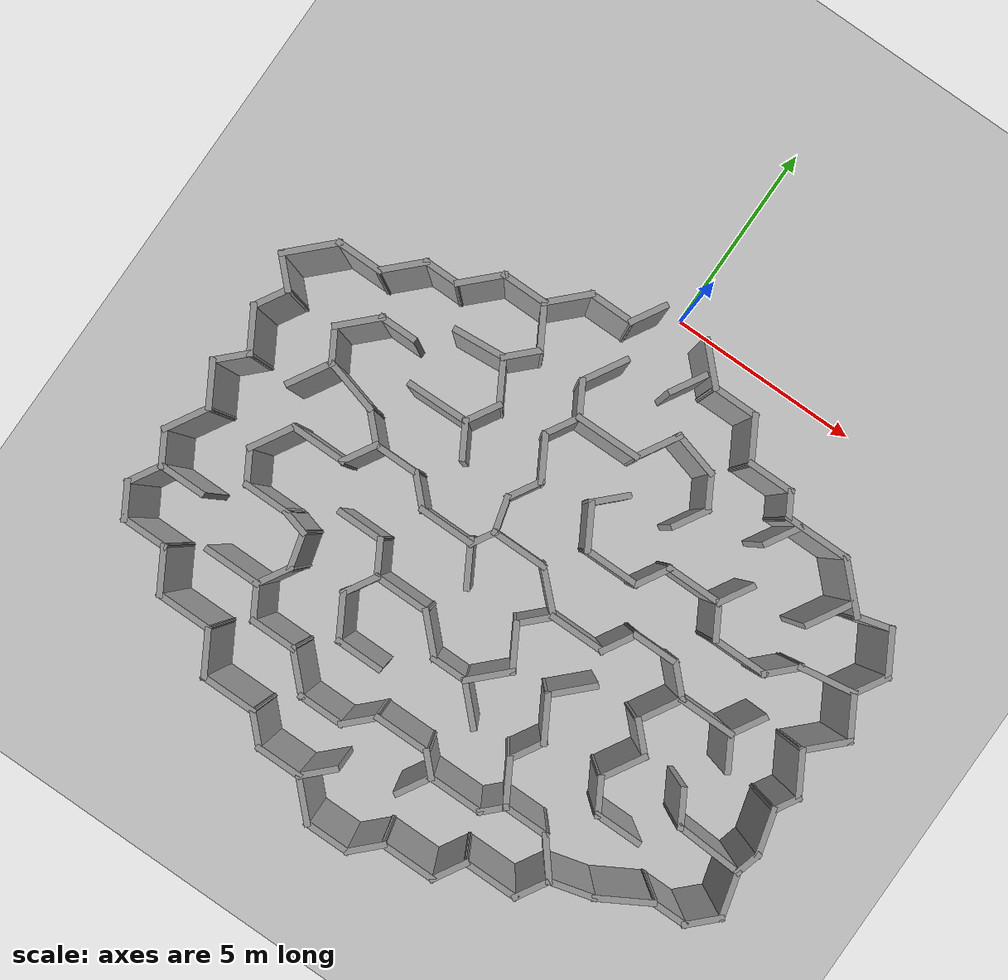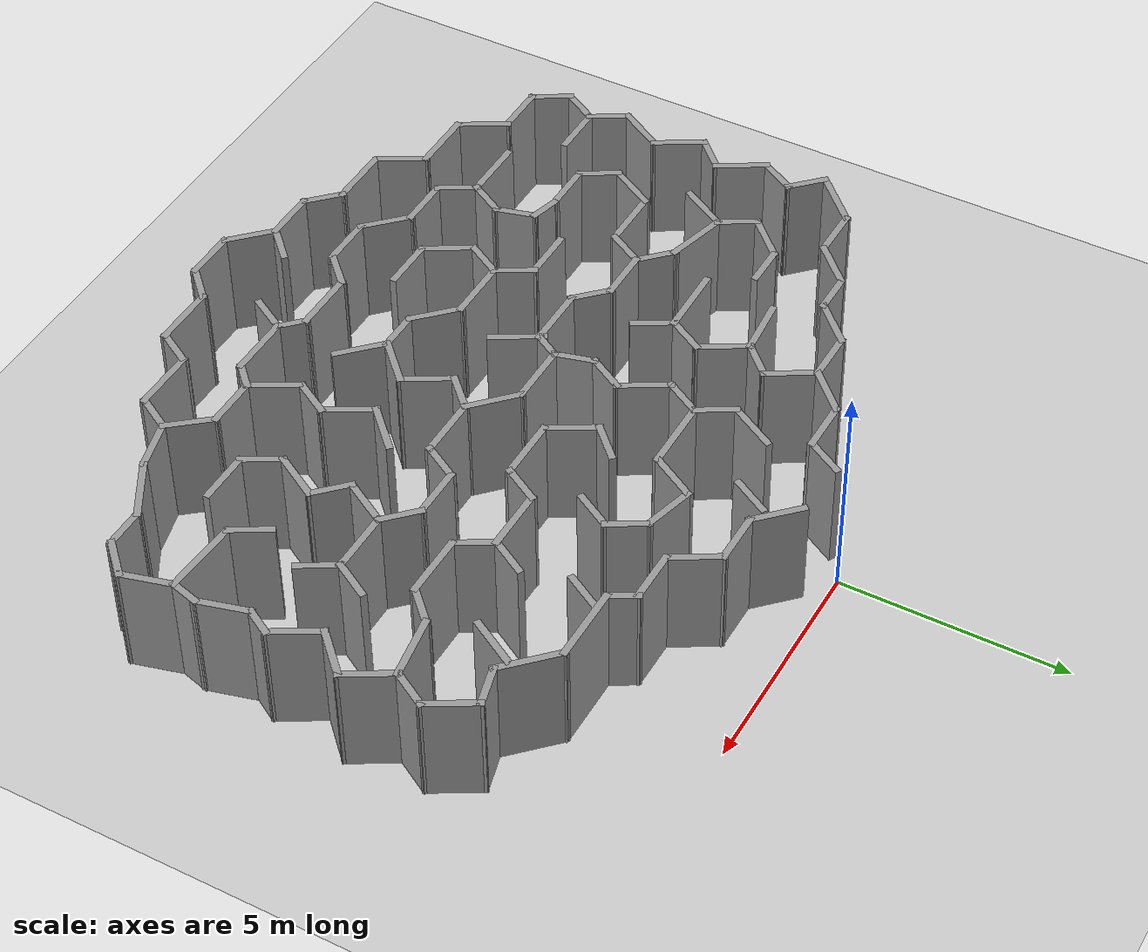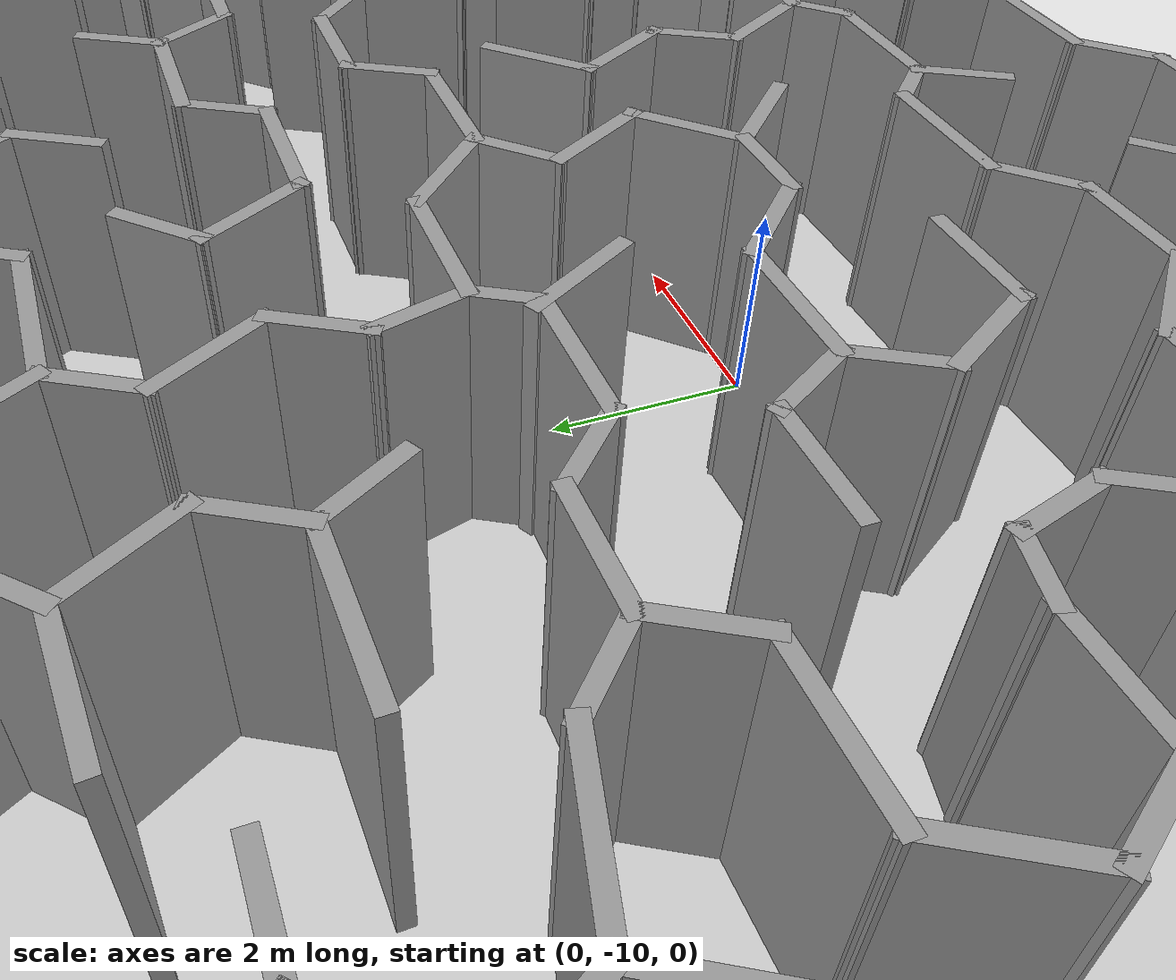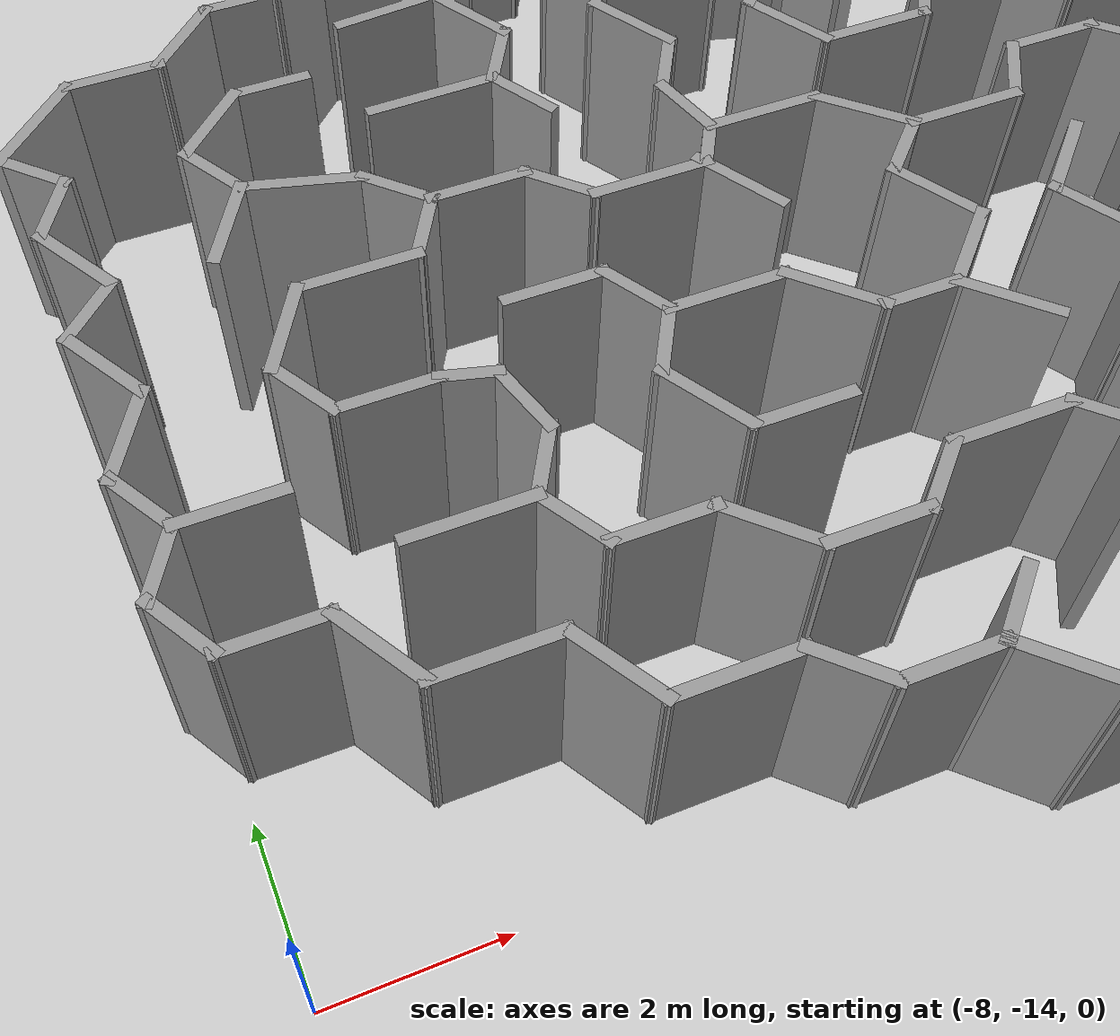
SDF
<sdf version="1.7">
 <world name="default">
  <light name="sun" type="directional">
   <pose>0 0 10 0 -0 0</pose>
   <diffuse>0.8 0.8 0.8 1</diffuse>
   <specular>0.2 0.2 0.2 1</specular>
   <attenuation>
    <range>1000</range>
    <constant>0.9</constant>
    <linear>0.01</linear>
    <quadratic>0.001</quadratic>
   </attenuation>
   <direction>-0.5 0.1 -0.9</direction>
   <spot><inner_angle>0</inner_angle><outer_angle>0</outer_angle><falloff>0</falloff></spot>
  </light>
  <model name="ground_plane">
   <static>1</static>
   <link name="link">
    <collision name="collision">
     <geometry><plane><normal>0 0 1</normal><size>100 100</size></plane></geometry>
     <surface><friction><ode><mu>100</mu><mu2>50</mu2></ode></friction></surface>
    </collision>
    <visual name="visual">
     <cast_shadows>0</cast_shadows>
     <geometry><plane><normal>0 0 1</normal><size>100 100</size></plane></geometry>
     <material>
      <script><uri>file://media/materials/scripts/gazebo.material</uri><name>Gazebo/Grey</name></script>
     </material>
    </visual>
   </link>
  </model>
  <gravity>0 0 -9.8</gravity>
  <magnetic_field>6e-06 2.3e-05 -4.2e-05</magnetic_field>
  <atmosphere type="adiabatic"/>
  <physics type="ode">
   <max_step_size>0.001</max_step_size>
   <real_time_factor>1</real_time_factor>
   <real_time_update_rate>1000</real_time_update_rate>
  </physics>
  <scene><ambient>0.4 0.4 0.4 1</ambient><background>0.7 0.7 0.7 1</background><shadows>1</shadows></scene>
  <audio><device>default</device></audio>
  <spherical_coordinates>
   <surface_model>EARTH_WGS84</surface_model>
   <latitude_deg>0</latitude_deg>
   <longitude_deg>0</longitude_deg>
   <elevation>0</elevation>
   <heading_deg>0</heading_deg>
  </spherical_coordinates>
  <model name="Maze">
   <pose>0.084887 -7.59379 0 0 -0 0</pose>
   <link name="Wall_1">
    <collision name="Wall_1_Collision">
     <geometry><box><size>1 0.15 2.5</size></box></geometry>
     <pose>0 0 1.25 0 -0 0</pose>
    </collision>
    <visual name="Wall_1_Visual">
     <pose>0 0 1.25 0 -0 0</pose>
     <geometry><box><size>1 0.15 2.5</size></box></geometry>
     <material>
      <script><uri>file://media/materials/scripts/gazebo.material</uri><name>Gazebo/Grey</name></script>
      <ambient>1 1 1 1</ambient>
     </material>
     <meta><layer>0</layer></meta>
    </visual>
    <pose>-0.837603 6.79011 0 0 -0 -2.0944</pose>
   </link>
   <link name="Wall_10">
    <collision name="Wall_10_Collision">
     <geometry><box><size>1 0.15 2.5</size></box></geometry>
     <pose>0 0 1.25 0 -0 0</pose>
    </collision>
    <visual name="Wall_10_Visual">
     <pose>0 0 1.25 0 -0 0</pose>
     <geometry><box><size>1 0.15 2.5</size></box></geometry>
     <material>
      <script><uri>file://media/materials/scripts/gazebo.material</uri><name>Gazebo/Grey</name></script>
      <ambient>1 1 1 1</ambient>
     </material>
     <meta><layer>0</layer></meta>
    </visual>
    <pose>-8.18763 2.83349 0 0 -0 -0.785398</pose>
   </link>
   <link name="Wall_100">
    <collision name="Wall_100_Collision">
     <geometry><box><size>0.75 0.15 2.5</size></box></geometry>
     <pose>0 0 1.25 0 -0 0</pose>
    </collision>
    <visual name="Wall_100_Visual">
     <pose>0 0 1.25 0 -0 0</pose>
     <geometry><box><size>0.75 0.15 2.5</size></box></geometry>
     <material>
      <script><uri>file://media/materials/scripts/gazebo.material</uri><name>Gazebo/Grey</name></script>
      <ambient>1 1 1 1</ambient>
     </material>
     <meta><layer>0</layer></meta>
    </visual>
    <pose>-4.7111 -1.71873 0 0 -0 -0.261799</pose>
   </link>
   <link name="Wall_101">
    <collision name="Wall_101_Collision">
     <geometry><box><size>1 0.15 2.5</size></box></geometry>
     <pose>0 0 1.25 0 -0 0</pose>
    </collision>
    <visual name="Wall_101_Visual">
     <pose>0 0 1.25 0 -0 0</pose>
     <geometry><box><size>1 0.15 2.5</size></box></geometry>
     <material>
      <script><uri>file://media/materials/scripts/gazebo.material</uri><name>Gazebo/Grey</name></script>
      <ambient>1 1 1 1</ambient>
     </material>
     <meta><layer>0</layer></meta>
    </visual>
    <pose>-4.31133 -2.20689 0 0 -0 -1.309</pose>
   </link>
   <link name="Wall_102">
    <collision name="Wall_102_Collision">
     <geometry><box><size>1 0.15 2.5</size></box></geometry>
     <pose>0 0 1.25 0 -0 0</pose>
    </collision>
    <visual name="Wall_102_Visual">
     <pose>0 0 1.25 0 -0 0</pose>
     <geometry><box><size>1 0.15 2.5</size></box></geometry>
     <material>
      <script><uri>file://media/materials/scripts/gazebo.material</uri><name>Gazebo/Grey</name></script>
      <ambient>1 1 1 1</ambient>
     </material>
     <meta><layer>0</layer></meta>
    </visual>
    <pose>-4.41383 -2.98547 0 0 -0 -2.0944</pose>
   </link>
   <link name="Wall_103">
    <collision name="Wall_103_Collision">
     <geometry><box><size>1.5 0.15 2.5</size></box></geometry>
     <pose>0 0 1.25 0 -0 0</pose>
    </collision>
    <visual name="Wall_103_Visual">
     <pose>0 0 1.25 0 -0 0</pose>
     <geometry><box><size>1.5 0.15 2.5</size></box></geometry>
     <material>
      <script><uri>file://media/materials/scripts/gazebo.material</uri><name>Gazebo/Grey</name></script>
      <ambient>1 1 1 1</ambient>
     </material>
     <meta><layer>0</layer></meta>
    </visual>
    <pose>-5.30133 -3.35353 0 0 -0 3.14159</pose>
   </link>
   <link name="Wall_105">
    <collision name="Wall_105_Collision">
     <geometry><box><size>1 0.15 2.5</size></box></geometry>
     <pose>0 0 1.25 0 -0 0</pose>
    </collision>
    <visual name="Wall_105_Visual">
     <pose>0 0 1.25 0 -0 0</pose>
     <geometry><box><size>1 0.15 2.5</size></box></geometry>
     <material>
      <script><uri>file://media/materials/scripts/gazebo.material</uri><name>Gazebo/Grey</name></script>
      <ambient>1 1 1 1</ambient>
     </material>
     <meta><layer>0</layer></meta>
    </visual>
    <pose>-4.41383 -3.72159 0 0 -0 -1.0472</pose>
   </link>
   <link name="Wall_106">
    <collision name="Wall_106_Collision">
     <geometry><box><size>1.25 0.15 2.5</size></box></geometry>
     <pose>0 0 1.25 0 -0 0</pose>
    </collision>
    <visual name="Wall_106_Visual">
     <pose>0 0 1.25 0 -0 0</pose>
     <geometry><box><size>1.25 0.15 2.5</size></box></geometry>
     <material>
      <script><uri>file://media/materials/scripts/gazebo.material</uri><name>Gazebo/Grey</name></script>
      <ambient>1 1 1 1</ambient>
     </material>
     <meta><layer>0</layer></meta>
    </visual>
    <pose>-3.65133 -4.08965 0 0 -0 0</pose>
   </link>
   <link name="Wall_107">
    <collision name="Wall_107_Collision">
     <geometry><box><size>1.25 0.15 2.5</size></box></geometry>
     <pose>0 0 1.25 0 -0 0</pose>
    </collision>
    <visual name="Wall_107_Visual">
     <pose>0 0 1.25 0 -0 0</pose>
     <geometry><box><size>1.25 0.15 2.5</size></box></geometry>
     <material>
      <script><uri>file://media/materials/scripts/gazebo.material</uri><name>Gazebo/Grey</name></script>
      <ambient>1 1 1 1</ambient>
     </material>
     <meta><layer>0</layer></meta>
    </visual>
    <pose>-2.71242 -4.47856 0 0 -0 -0.785398</pose>
   </link>
   <link name="Wall_108">
    <collision name="Wall_108_Collision">
     <geometry><box><size>1.25 0.15 2.5</size></box></geometry>
     <pose>0 0 1.25 0 -0 0</pose>
    </collision>
    <visual name="Wall_108_Visual">
     <pose>0 0 1.25 0 -0 0</pose>
     <geometry><box><size>1.25 0.15 2.5</size></box></geometry>
     <material>
      <script><uri>file://media/materials/scripts/gazebo.material</uri><name>Gazebo/Grey</name></script>
      <ambient>1 1 1 1</ambient>
     </material>
     <meta><layer>0</layer></meta>
    </visual>
    <pose>-1.77351 -4.86747 0 0 -0 0</pose>
   </link>
   <link name="Wall_109">
    <collision name="Wall_109_Collision">
     <geometry><box><size>1 0.15 2.5</size></box></geometry>
     <pose>0 0 1.25 0 -0 0</pose>
    </collision>
    <visual name="Wall_109_Visual">
     <pose>0 0 1.25 0 -0 0</pose>
     <geometry><box><size>1 0.15 2.5</size></box></geometry>
     <material>
      <script><uri>file://media/materials/scripts/gazebo.material</uri><name>Gazebo/Grey</name></script>
      <ambient>1 1 1 1</ambient>
     </material>
     <meta><layer>0</layer></meta>
    </visual>
    <pose>-0.92299 -4.56695 0 0 -0 0.785398</pose>
   </link>
   <link name="Wall_11">
    <collision name="Wall_11_Collision">
     <geometry><box><size>1 0.15 2.5</size></box></geometry>
     <pose>0 0 1.25 0 -0 0</pose>
    </collision>
    <visual name="Wall_11_Visual">
     <pose>0 0 1.25 0 -0 0</pose>
     <geometry><box><size>1 0.15 2.5</size></box></geometry>
     <material>
      <script><uri>file://media/materials/scripts/gazebo.material</uri><name>Gazebo/Grey</name></script>
      <ambient>1 1 1 1</ambient>
     </material>
     <meta><layer>0</layer></meta>
    </visual>
    <pose>-8.09961 2.1649 0 0 -0 -2.0944</pose>
   </link>
   <link name="Wall_110">
    <collision name="Wall_110_Collision">
     <geometry><box><size>1.5 0.15 2.5</size></box></geometry>
     <pose>0 0 1.25 0 -0 0</pose>
    </collision>
    <visual name="Wall_110_Visual">
     <pose>0 0 1.25 0 -0 0</pose>
     <geometry><box><size>1.5 0.15 2.5</size></box></geometry>
     <material>
      <script><uri>file://media/materials/scripts/gazebo.material</uri><name>Gazebo/Grey</name></script>
      <ambient>1 1 1 1</ambient>
     </material>
     <meta><layer>0</layer></meta>
    </visual>
    <pose>0.05253 -4.26643 0 0 -0 0</pose>
   </link>
   <link name="Wall_111">
    <collision name="Wall_111_Collision">
     <geometry><box><size>0.75 0.15 2.5</size></box></geometry>
     <pose>0 0 1.25 0 -0 0</pose>
    </collision>
    <visual name="Wall_111_Visual">
     <pose>0 0 1.25 0 -0 0</pose>
     <geometry><box><size>0.75 0.15 2.5</size></box></geometry>
     <material>
      <script><uri>file://media/materials/scripts/gazebo.material</uri><name>Gazebo/Grey</name></script>
      <ambient>1 1 1 1</ambient>
     </material>
     <meta><layer>0</layer></meta>
    </visual>
    <pose>0.939662 -4.47856 0 0 -0 -0.785398</pose>
   </link>
   <link name="Wall_112">
    <collision name="Wall_112_Collision">
     <geometry><box><size>1 0.15 2.5</size></box></geometry>
     <pose>0 0 1.25 0 -0 0</pose>
    </collision>
    <visual name="Wall_112_Visual">
     <pose>0 0 1.25 0 -0 0</pose>
     <geometry><box><size>1 0.15 2.5</size></box></geometry>
     <material>
      <script><uri>file://media/materials/scripts/gazebo.material</uri><name>Gazebo/Grey</name></script>
      <ambient>1 1 1 1</ambient>
     </material>
     <meta><layer>0</layer></meta>
    </visual>
    <pose>0.939294 -5.05876 0 0 -0 -2.0944</pose>
   </link>
   <link name="Wall_114">
    <collision name="Wall_114_Collision">
     <geometry><box><size>1.5 0.15 2.5</size></box></geometry>
     <pose>0 0 1.25 0 -0 0</pose>
    </collision>
    <visual name="Wall_114_Visual">
     <pose>0 0 1.25 0 -0 0</pose>
     <geometry><box><size>1.5 0.15 2.5</size></box></geometry>
     <material>
      <script><uri>file://media/materials/scripts/gazebo.material</uri><name>Gazebo/Grey</name></script>
      <ambient>1 1 1 1</ambient>
     </material>
     <meta><layer>0</layer></meta>
    </visual>
    <pose>1.82679 -4.69069 0 0 -0 0</pose>
   </link>
   <link name="Wall_115">
    <collision name="Wall_115_Collision">
     <geometry><box><size>0.75 0.15 2.5</size></box></geometry>
     <pose>0 0 1.25 0 -0 0</pose>
    </collision>
    <visual name="Wall_115_Visual">
     <pose>0 0 1.25 0 -0 0</pose>
     <geometry><box><size>0.75 0.15 2.5</size></box></geometry>
     <material>
      <script><uri>file://media/materials/scripts/gazebo.material</uri><name>Gazebo/Grey</name></script>
      <ambient>1 1 1 1</ambient>
     </material>
     <meta><layer>0</layer></meta>
    </visual>
    <pose>2.71393 -4.47856 0 0 -0 0.785398</pose>
   </link>
   <link name="Wall_116">
    <collision name="Wall_116_Collision">
     <geometry><box><size>1.25 0.15 2.5</size></box></geometry>
     <pose>0 0 1.25 0 -0 0</pose>
    </collision>
    <visual name="Wall_116_Visual">
     <pose>0 0 1.25 0 -0 0</pose>
     <geometry><box><size>1.25 0.15 2.5</size></box></geometry>
     <material>
      <script><uri>file://media/materials/scripts/gazebo.material</uri><name>Gazebo/Grey</name></script>
      <ambient>1 1 1 1</ambient>
     </material>
     <meta><layer>0</layer></meta>
    </visual>
    <pose>2.65106 -3.79012 0 0 -0 2.0944</pose>
   </link>
   <link name="Wall_117">
    <collision name="Wall_117_Collision">
     <geometry><box><size>1 0.15 2.5</size></box></geometry>
     <pose>0 0 1.25 0 -0 0</pose>
    </collision>
    <visual name="Wall_117_Visual">
     <pose>0 0 1.25 0 -0 0</pose>
     <geometry><box><size>1 0.15 2.5</size></box></geometry>
     <material>
      <script><uri>file://media/materials/scripts/gazebo.material</uri><name>Gazebo/Grey</name></script>
      <ambient>1 1 1 1</ambient>
     </material>
     <meta><layer>0</layer></meta>
    </visual>
    <pose>2.58856 -2.94574 0 0 -0 1.0472</pose>
   </link>
   <link name="Wall_118">
    <collision name="Wall_118_Collision">
     <geometry><box><size>1.25 0.15 2.5</size></box></geometry>
     <pose>0 0 1.25 0 -0 0</pose>
    </collision>
    <visual name="Wall_118_Visual">
     <pose>0 0 1.25 0 -0 0</pose>
     <geometry><box><size>1.25 0.15 2.5</size></box></geometry>
     <material>
      <script><uri>file://media/materials/scripts/gazebo.material</uri><name>Gazebo/Grey</name></script>
      <ambient>1 1 1 1</ambient>
     </material>
     <meta><layer>0</layer></meta>
    </visual>
    <pose>2.52606 -2.10137 0 0 -0 2.0944</pose>
   </link>
   <link name="Wall_119">
    <collision name="Wall_119_Collision">
     <geometry><box><size>1.25 0.15 2.5</size></box></geometry>
     <pose>0 0 1.25 0 -0 0</pose>
    </collision>
    <visual name="Wall_119_Visual">
     <pose>0 0 1.25 0 -0 0</pose>
     <geometry><box><size>1.25 0.15 2.5</size></box></geometry>
     <material>
      <script><uri>file://media/materials/scripts/gazebo.material</uri><name>Gazebo/Grey</name></script>
      <ambient>1 1 1 1</ambient>
     </material>
     <meta><layer>0</layer></meta>
    </visual>
    <pose>2.63997 -1.23615 0 0 -0 0.785398</pose>
   </link>
   <link name="Wall_12">
    <collision name="Wall_12_Collision">
     <geometry><box><size>1.25 0.15 2.5</size></box></geometry>
     <pose>0 0 1.25 0 -0 0</pose>
    </collision>
    <visual name="Wall_12_Visual">
     <pose>0 0 1.25 0 -0 0</pose>
     <geometry><box><size>1.25 0.15 2.5</size></box></geometry>
     <material>
      <script><uri>file://media/materials/scripts/gazebo.material</uri><name>Gazebo/Grey</name></script>
      <ambient>1 1 1 1</ambient>
     </material>
     <meta><layer>0</layer></meta>
    </visual>
    <pose>-8.03711 1.32053 0 0 -0 -1.0472</pose>
   </link>
   <link name="Wall_121">
    <collision name="Wall_121_Collision">
     <geometry><box><size>1.25 0.15 2.5</size></box></geometry>
     <pose>0 0 1.25 0 -0 0</pose>
    </collision>
    <visual name="Wall_121_Visual">
     <pose>0 0 1.25 0 -0 0</pose>
     <geometry><box><size>1.25 0.15 2.5</size></box></geometry>
     <material>
      <script><uri>file://media/materials/scripts/gazebo.material</uri><name>Gazebo/Grey</name></script>
      <ambient>1 1 1 1</ambient>
     </material>
     <meta><layer>0</layer></meta>
    </visual>
    <pose>3.47606 -4.26643 0 0 -0 0</pose>
   </link>
   <link name="Wall_122">
    <collision name="Wall_122_Collision">
     <geometry><box><size>1.2022 0.15 2.5</size></box></geometry>
     <pose>0 0 1.25 0 -0 0</pose>
    </collision>
    <visual name="Wall_122_Visual">
     <pose>0 0 1.25 0 -0 0</pose>
     <geometry><box><size>1.2022 0.15 2.5</size></box></geometry>
     <material>
      <script><uri>file://media/materials/scripts/gazebo.material</uri><name>Gazebo/Grey</name></script>
      <ambient>1 1 1 1</ambient>
     </material>
     <meta><layer>0</layer></meta>
    </visual>
    <pose>4.3589 -4.67385 0 0 -0 -0.885802</pose>
   </link>
   <link name="Wall_124">
    <collision name="Wall_124_Collision">
     <geometry><box><size>1 0.15 2.5</size></box></geometry>
     <pose>0 0 1.25 0 -0 0</pose>
    </collision>
    <visual name="Wall_124_Visual">
     <pose>0 0 1.25 0 -0 0</pose>
     <geometry><box><size>1 0.15 2.5</size></box></geometry>
     <material>
      <script><uri>file://media/materials/scripts/gazebo.material</uri><name>Gazebo/Grey</name></script>
      <ambient>1 1 1 1</ambient>
     </material>
     <meta><layer>0</layer></meta>
    </visual>
    <pose>0.864304 2.83096 0 0 -0 -2.35619</pose>
   </link>
   <link name="Wall_125">
    <collision name="Wall_125_Collision">
     <geometry><box><size>1.25 0.15 2.5</size></box></geometry>
     <pose>0 0 1.25 0 -0 0</pose>
    </collision>
    <visual name="Wall_125_Visual">
     <pose>0 0 1.25 0 -0 0</pose>
     <geometry><box><size>1.25 0.15 2.5</size></box></geometry>
     <material>
      <script><uri>file://media/materials/scripts/gazebo.material</uri><name>Gazebo/Grey</name></script>
      <ambient>1 1 1 1</ambient>
     </material>
     <meta><layer>0</layer></meta>
    </visual>
    <pose>0.838784 2.05413 0 0 -0 -1.0472</pose>
   </link>
   <link name="Wall_126">
    <collision name="Wall_126_Collision">
     <geometry><box><size>1.5 0.15 2.5</size></box></geometry>
     <pose>0 0 1.25 0 -0 0</pose>
    </collision>
    <visual name="Wall_126_Visual">
     <pose>0 0 1.25 0 -0 0</pose>
     <geometry><box><size>1.5 0.15 2.5</size></box></geometry>
     <material>
      <script><uri>file://media/materials/scripts/gazebo.material</uri><name>Gazebo/Grey</name></script>
      <ambient>1 1 1 1</ambient>
     </material>
     <meta><layer>0</layer></meta>
    </visual>
    <pose>1.78878 1.57782 0 0 -0 0</pose>
   </link>
   <link name="Wall_127">
    <collision name="Wall_127_Collision">
     <geometry><box><size>1 0.15 2.5</size></box></geometry>
     <pose>0 0 1.25 0 -0 0</pose>
    </collision>
    <visual name="Wall_127_Visual">
     <pose>0 0 1.25 0 -0 0</pose>
     <geometry><box><size>1 0.15 2.5</size></box></geometry>
     <material>
      <script><uri>file://media/materials/scripts/gazebo.material</uri><name>Gazebo/Grey</name></script>
      <ambient>1 1 1 1</ambient>
     </material>
     <meta><layer>0</layer></meta>
    </visual>
    <pose>2.67628 1.94588 0 0 -0 1.0472</pose>
   </link>
   <link name="Wall_128">
    <collision name="Wall_128_Collision">
     <geometry><box><size>1.5 0.15 2.5</size></box></geometry>
     <pose>0 0 1.25 0 -0 0</pose>
    </collision>
    <visual name="Wall_128_Visual">
     <pose>0 0 1.25 0 -0 0</pose>
     <geometry><box><size>1.5 0.15 2.5</size></box></geometry>
     <material>
      <script><uri>file://media/materials/scripts/gazebo.material</uri><name>Gazebo/Grey</name></script>
      <ambient>1 1 1 1</ambient>
     </material>
     <meta><layer>0</layer></meta>
    </visual>
    <pose>3.56378 2.31394 0 0 -0 0</pose>
   </link>
   <link name="Wall_129">
    <collision name="Wall_129_Collision">
     <geometry><box><size>1 0.15 2.5</size></box></geometry>
     <pose>0 0 1.25 0 -0 0</pose>
    </collision>
    <visual name="Wall_129_Visual">
     <pose>0 0 1.25 0 -0 0</pose>
     <geometry><box><size>1 0.15 2.5</size></box></geometry>
     <material>
      <script><uri>file://media/materials/scripts/gazebo.material</uri><name>Gazebo/Grey</name></script>
      <ambient>1 1 1 1</ambient>
     </material>
     <meta><layer>0</layer></meta>
    </visual>
    <pose>4.45128 2.682 0 0 -0 1.0472</pose>
   </link>
   <link name="Wall_13">
    <collision name="Wall_13_Collision">
     <geometry><box><size>1 0.15 2.5</size></box></geometry>
     <pose>0 0 1.25 0 -0 0</pose>
    </collision>
    <visual name="Wall_13_Visual">
     <pose>0 0 1.25 0 -0 0</pose>
     <geometry><box><size>1 0.15 2.5</size></box></geometry>
     <material>
      <script><uri>file://media/materials/scripts/gazebo.material</uri><name>Gazebo/Grey</name></script>
      <ambient>1 1 1 1</ambient>
     </material>
     <meta><layer>0</layer></meta>
    </visual>
    <pose>-8.06263 0.543695 0 0 -0 -2.35619</pose>
   </link>
   <link name="Wall_131">
    <collision name="Wall_131_Collision">
     <geometry><box><size>1 0.15 2.5</size></box></geometry>
     <pose>0 0 1.25 0 -0 0</pose>
    </collision>
    <visual name="Wall_131_Visual">
     <pose>0 0 1.25 0 -0 0</pose>
     <geometry><box><size>1 0.15 2.5</size></box></geometry>
     <material>
      <script><uri>file://media/materials/scripts/gazebo.material</uri><name>Gazebo/Grey</name></script>
      <ambient>1 1 1 1</ambient>
     </material>
     <meta><layer>0</layer></meta>
    </visual>
    <pose>4.45128 1.94588 0 0 -0 -1.0472</pose>
   </link>
   <link name="Wall_132">
    <collision name="Wall_132_Collision">
     <geometry><box><size>1.5 0.15 2.5</size></box></geometry>
     <pose>0 0 1.25 0 -0 0</pose>
    </collision>
    <visual name="Wall_132_Visual">
     <pose>0 0 1.25 0 -0 0</pose>
     <geometry><box><size>1.5 0.15 2.5</size></box></geometry>
     <material>
      <script><uri>file://media/materials/scripts/gazebo.material</uri><name>Gazebo/Grey</name></script>
      <ambient>1 1 1 1</ambient>
     </material>
     <meta><layer>0</layer></meta>
    </visual>
    <pose>5.33878 1.57782 0 0 -0 0</pose>
   </link>
   <link name="Wall_133">
    <collision name="Wall_133_Collision">
     <geometry><box><size>1 0.15 2.5</size></box></geometry>
     <pose>0 0 1.25 0 -0 0</pose>
    </collision>
    <visual name="Wall_133_Visual">
     <pose>0 0 1.25 0 -0 0</pose>
     <geometry><box><size>1 0.15 2.5</size></box></geometry>
     <material>
      <script><uri>file://media/materials/scripts/gazebo.material</uri><name>Gazebo/Grey</name></script>
      <ambient>1 1 1 1</ambient>
     </material>
     <meta><layer>0</layer></meta>
    </visual>
    <pose>6.3143 1.87834 0 0 -0 0.785398</pose>
   </link>
   <link name="Wall_134">
    <collision name="Wall_134_Collision">
     <geometry><box><size>1.48955 0.15 2.5</size></box></geometry>
     <pose>0 0 1.25 0 -0 0</pose>
    </collision>
    <visual name="Wall_134_Visual">
     <pose>0 0 1.25 0 -0 0</pose>
     <geometry><box><size>1.48955 0.15 2.5</size></box></geometry>
     <material>
      <script><uri>file://media/materials/scripts/gazebo.material</uri><name>Gazebo/Grey</name></script>
      <ambient>1 1 1 1</ambient>
     </material>
     <meta><layer>0</layer></meta>
    </visual>
    <pose>7.27649 2.2828 0 0 -0 0.155823</pose>
   </link>
   <link name="Wall_136">
    <collision name="Wall_136_Collision">
     <geometry><box><size>1 0.15 2.5</size></box></geometry>
     <pose>0 0 1.25 0 -0 0</pose>
    </collision>
    <visual name="Wall_136_Visual">
     <pose>0 0 1.25 0 -0 0</pose>
     <geometry><box><size>1 0.15 2.5</size></box></geometry>
     <material>
      <script><uri>file://media/materials/scripts/gazebo.material</uri><name>Gazebo/Grey</name></script>
      <ambient>1 1 1 1</ambient>
     </material>
     <meta><layer>0</layer></meta>
    </visual>
    <pose>6.38032 0.394424 0 0 -0 -2.0944</pose>
   </link>
   <link name="Wall_137">
    <collision name="Wall_137_Collision">
     <geometry><box><size>1 0.15 2.5</size></box></geometry>
     <pose>0 0 1.25 0 -0 0</pose>
    </collision>
    <visual name="Wall_137_Visual">
     <pose>0 0 1.25 0 -0 0</pose>
     <geometry><box><size>1 0.15 2.5</size></box></geometry>
     <material>
      <script><uri>file://media/materials/scripts/gazebo.material</uri><name>Gazebo/Grey</name></script>
      <ambient>1 1 1 1</ambient>
     </material>
     <meta><layer>0</layer></meta>
    </visual>
    <pose>6.38032 -0.341698 0 0 -0 -1.0472</pose>
   </link>
   <link name="Wall_139">
    <collision name="Wall_139_Collision">
     <geometry><box><size>1.5 0.15 2.5</size></box></geometry>
     <pose>0 0 1.25 0 -0 0</pose>
    </collision>
    <visual name="Wall_139_Visual">
     <pose>0 0 1.25 0 -0 0</pose>
     <geometry><box><size>1.5 0.15 2.5</size></box></geometry>
     <material>
      <script><uri>file://media/materials/scripts/gazebo.material</uri><name>Gazebo/Grey</name></script>
      <ambient>1 1 1 1</ambient>
     </material>
     <meta><layer>0</layer></meta>
    </visual>
    <pose>5.49282 0.026363 0 0 -0 3.14159</pose>
   </link>
   <link name="Wall_14">
    <collision name="Wall_14_Collision">
     <geometry><box><size>1.25 0.15 2.5</size></box></geometry>
     <pose>0 0 1.25 0 -0 0</pose>
    </collision>
    <visual name="Wall_14_Visual">
     <pose>0 0 1.25 0 -0 0</pose>
     <geometry><box><size>1.25 0.15 2.5</size></box></geometry>
     <material>
      <script><uri>file://media/materials/scripts/gazebo.material</uri><name>Gazebo/Grey</name></script>
      <ambient>1 1 1 1</ambient>
     </material>
     <meta><layer>0</layer></meta>
    </visual>
    <pose>-8.08815 -0.233139 0 0 -0 -1.0472</pose>
   </link>
   <link name="Wall_140">
    <collision name="Wall_140_Collision">
     <geometry><box><size>1 0.15 2.5</size></box></geometry>
     <pose>0 0 1.25 0 -0 0</pose>
    </collision>
    <visual name="Wall_140_Visual">
     <pose>0 0 1.25 0 -0 0</pose>
     <geometry><box><size>1 0.15 2.5</size></box></geometry>
     <material>
      <script><uri>file://media/materials/scripts/gazebo.material</uri><name>Gazebo/Grey</name></script>
      <ambient>1 1 1 1</ambient>
     </material>
     <meta><layer>0</layer></meta>
    </visual>
    <pose>4.5173 0.326883 0 0 -0 2.35619</pose>
   </link>
   <link name="Wall_141">
    <collision name="Wall_141_Collision">
     <geometry><box><size>1.25 0.15 2.5</size></box></geometry>
     <pose>0 0 1.25 0 -0 0</pose>
    </collision>
    <visual name="Wall_141_Visual">
     <pose>0 0 1.25 0 -0 0</pose>
     <geometry><box><size>1.25 0.15 2.5</size></box></geometry>
     <material>
      <script><uri>file://media/materials/scripts/gazebo.material</uri><name>Gazebo/Grey</name></script>
      <ambient>1 1 1 1</ambient>
     </material>
     <meta><layer>0</layer></meta>
    </visual>
    <pose>3.66678 0.627404 0 0 -0 3.14159</pose>
   </link>
   <link name="Wall_142">
    <collision name="Wall_142_Collision">
     <geometry><box><size>1 0.15 2.5</size></box></geometry>
     <pose>0 0 1.25 0 -0 0</pose>
    </collision>
    <visual name="Wall_142_Visual">
     <pose>0 0 1.25 0 -0 0</pose>
     <geometry><box><size>1 0.15 2.5</size></box></geometry>
     <material>
      <script><uri>file://media/materials/scripts/gazebo.material</uri><name>Gazebo/Grey</name></script>
      <ambient>1 1 1 1</ambient>
     </material>
     <meta><layer>0</layer></meta>
    </visual>
    <pose>2.90428 0.259343 0 0 -0 -2.0944</pose>
   </link>
   <link name="Wall_143">
    <collision name="Wall_143_Collision">
     <geometry><box><size>1.5 0.15 2.5</size></box></geometry>
     <pose>0 0 1.25 0 -0 0</pose>
    </collision>
    <visual name="Wall_143_Visual">
     <pose>0 0 1.25 0 -0 0</pose>
     <geometry><box><size>1.5 0.15 2.5</size></box></geometry>
     <material>
      <script><uri>file://media/materials/scripts/gazebo.material</uri><name>Gazebo/Grey</name></script>
      <ambient>1 1 1 1</ambient>
     </material>
     <meta><layer>0</layer></meta>
    </visual>
    <pose>2.01678 -0.108718 0 0 -0 3.14159</pose>
   </link>
   <link name="Wall_144">
    <collision name="Wall_144_Collision">
     <geometry><box><size>1 0.15 2.5</size></box></geometry>
     <pose>0 0 1.25 0 -0 0</pose>
    </collision>
    <visual name="Wall_144_Visual">
     <pose>0 0 1.25 0 -0 0</pose>
     <geometry><box><size>1 0.15 2.5</size></box></geometry>
     <material>
      <script><uri>file://media/materials/scripts/gazebo.material</uri><name>Gazebo/Grey</name></script>
      <ambient>1 1 1 1</ambient>
     </material>
     <meta><layer>0</layer></meta>
    </visual>
    <pose>1.04126 -0.409238 0 0 -0 -2.35619</pose>
   </link>
   <link name="Wall_145">
    <collision name="Wall_145_Collision">
     <geometry><box><size>1.25 0.15 2.5</size></box></geometry>
     <pose>0 0 1.25 0 -0 0</pose>
    </collision>
    <visual name="Wall_145_Visual">
     <pose>0 0 1.25 0 -0 0</pose>
     <geometry><box><size>1.25 0.15 2.5</size></box></geometry>
     <material>
      <script><uri>file://media/materials/scripts/gazebo.material</uri><name>Gazebo/Grey</name></script>
      <ambient>1 1 1 1</ambient>
     </material>
     <meta><layer>0</layer></meta>
    </visual>
    <pose>1.01574 -1.18607 0 0 -0 -1.0472</pose>
   </link>
   <link name="Wall_146">
    <collision name="Wall_146_Collision">
     <geometry><box><size>1.25 0.15 2.5</size></box></geometry>
     <pose>0 0 1.25 0 -0 0</pose>
    </collision>
    <visual name="Wall_146_Visual">
     <pose>0 0 1.25 0 -0 0</pose>
     <geometry><box><size>1.25 0.15 2.5</size></box></geometry>
     <material>
      <script><uri>file://media/materials/scripts/gazebo.material</uri><name>Gazebo/Grey</name></script>
      <ambient>1 1 1 1</ambient>
     </material>
     <meta><layer>0</layer></meta>
    </visual>
    <pose>0.901834 -2.0513 0 0 -0 -2.35619</pose>
   </link>
   <link name="Wall_147">
    <collision name="Wall_147_Collision">
     <geometry><box><size>1.25 0.15 2.5</size></box></geometry>
     <pose>0 0 1.25 0 -0 0</pose>
    </collision>
    <visual name="Wall_147_Visual">
     <pose>0 0 1.25 0 -0 0</pose>
     <geometry><box><size>1.25 0.15 2.5</size></box></geometry>
     <material>
      <script><uri>file://media/materials/scripts/gazebo.material</uri><name>Gazebo/Grey</name></script>
      <ambient>1 1 1 1</ambient>
     </material>
     <meta><layer>0</layer></meta>
    </visual>
    <pose>0.901834 -2.82911 0 0 -0 -0.785398</pose>
   </link>
   <link name="Wall_149">
    <collision name="Wall_149_Collision">
     <geometry><box><size>1 0.15 2.5</size></box></geometry>
     <pose>0 0 1.25 0 -0 0</pose>
    </collision>
    <visual name="Wall_149_Visual">
     <pose>0 0 1.25 0 -0 0</pose>
     <geometry><box><size>1 0.15 2.5</size></box></geometry>
     <material>
      <script><uri>file://media/materials/scripts/gazebo.material</uri><name>Gazebo/Grey</name></script>
      <ambient>1 1 1 1</ambient>
     </material>
     <meta><layer>0</layer></meta>
    </visual>
    <pose>0.087925 -2.4402 0 0 -0 3.14159</pose>
   </link>
   <link name="Wall_15">
    <collision name="Wall_15_Collision">
     <geometry><box><size>1.25 0.15 2.5</size></box></geometry>
     <pose>0 0 1.25 0 -0 0</pose>
    </collision>
    <visual name="Wall_15_Visual">
     <pose>0 0 1.25 0 -0 0</pose>
     <geometry><box><size>1.25 0.15 2.5</size></box></geometry>
     <material>
      <script><uri>file://media/materials/scripts/gazebo.material</uri><name>Gazebo/Grey</name></script>
      <ambient>1 1 1 1</ambient>
     </material>
     <meta><layer>0</layer></meta>
    </visual>
    <pose>-8.08815 -1.18577 0 0 -0 -2.0944</pose>
   </link>
   <link name="Wall_150">
    <collision name="Wall_150_Collision">
     <geometry><box><size>1.25 0.15 2.5</size></box></geometry>
     <pose>0 0 1.25 0 -0 0</pose>
    </collision>
    <visual name="Wall_150_Visual">
     <pose>0 0 1.25 0 -0 0</pose>
     <geometry><box><size>1.25 0.15 2.5</size></box></geometry>
     <material>
      <script><uri>file://media/materials/scripts/gazebo.material</uri><name>Gazebo/Grey</name></script>
      <ambient>1 1 1 1</ambient>
     </material>
     <meta><layer>0</layer></meta>
    </visual>
    <pose>-0.725983 -2.0513 0 0 -0 2.35619</pose>
   </link>
   <link name="Wall_151">
    <collision name="Wall_151_Collision">
     <geometry><box><size>1.5 0.15 2.5</size></box></geometry>
     <pose>0 0 1.25 0 -0 0</pose>
    </collision>
    <visual name="Wall_151_Visual">
     <pose>0 0 1.25 0 -0 0</pose>
     <geometry><box><size>1.5 0.15 2.5</size></box></geometry>
     <material>
      <script><uri>file://media/materials/scripts/gazebo.material</uri><name>Gazebo/Grey</name></script>
      <ambient>1 1 1 1</ambient>
     </material>
     <meta><layer>0</layer></meta>
    </visual>
    <pose>-1.78989 -1.66239 0 0 -0 3.14159</pose>
   </link>
   <link name="Wall_152">
    <collision name="Wall_152_Collision">
     <geometry><box><size>1 0.15 2.5</size></box></geometry>
     <pose>0 0 1.25 0 -0 0</pose>
    </collision>
    <visual name="Wall_152_Visual">
     <pose>0 0 1.25 0 -0 0</pose>
     <geometry><box><size>1 0.15 2.5</size></box></geometry>
     <material>
      <script><uri>file://media/materials/scripts/gazebo.material</uri><name>Gazebo/Grey</name></script>
      <ambient>1 1 1 1</ambient>
     </material>
     <meta><layer>0</layer></meta>
    </visual>
    <pose>-2.67739 -1.29433 0 0 -0 2.0944</pose>
   </link>
   <link name="Wall_153">
    <collision name="Wall_153_Collision">
     <geometry><box><size>1.25 0.15 2.5</size></box></geometry>
     <pose>0 0 1.25 0 -0 0</pose>
    </collision>
    <visual name="Wall_153_Visual">
     <pose>0 0 1.25 0 -0 0</pose>
     <geometry><box><size>1.25 0.15 2.5</size></box></geometry>
     <material>
      <script><uri>file://media/materials/scripts/gazebo.material</uri><name>Gazebo/Grey</name></script>
      <ambient>1 1 1 1</ambient>
     </material>
     <meta><layer>0</layer></meta>
    </visual>
    <pose>-3.43989 -0.926265 0 0 -0 3.14159</pose>
   </link>
   <link name="Wall_155">
    <collision name="Wall_155_Collision">
     <geometry><box><size>1 0.15 2.5</size></box></geometry>
     <pose>0 0 1.25 0 -0 0</pose>
    </collision>
    <visual name="Wall_155_Visual">
     <pose>0 0 1.25 0 -0 0</pose>
     <geometry><box><size>1 0.15 2.5</size></box></geometry>
     <material>
      <script><uri>file://media/materials/scripts/gazebo.material</uri><name>Gazebo/Grey</name></script>
      <ambient>1 1 1 1</ambient>
     </material>
     <meta><layer>0</layer></meta>
    </visual>
    <pose>-2.67739 -2.03045 0 0 -0 -2.0944</pose>
   </link>
   <link name="Wall_156">
    <collision name="Wall_156_Collision">
     <geometry><box><size>1.25 0.15 2.5</size></box></geometry>
     <pose>0 0 1.25 0 -0 0</pose>
    </collision>
    <visual name="Wall_156_Visual">
     <pose>0 0 1.25 0 -0 0</pose>
     <geometry><box><size>1.25 0.15 2.5</size></box></geometry>
     <material>
      <script><uri>file://media/materials/scripts/gazebo.material</uri><name>Gazebo/Grey</name></script>
      <ambient>1 1 1 1</ambient>
     </material>
     <meta><layer>0</layer></meta>
    </visual>
    <pose>-2.61489 -2.87482 0 0 -0 -1.0472</pose>
   </link>
   <link name="Wall_157">
    <collision name="Wall_157_Collision">
     <geometry><box><size>1.25 0.15 2.5</size></box></geometry>
     <pose>0 0 1.25 0 -0 0</pose>
    </collision>
    <visual name="Wall_157_Visual">
     <pose>0 0 1.25 0 -0 0</pose>
     <geometry><box><size>1.25 0.15 2.5</size></box></geometry>
     <material>
      <script><uri>file://media/materials/scripts/gazebo.material</uri><name>Gazebo/Grey</name></script>
      <ambient>1 1 1 1</ambient>
     </material>
     <meta><layer>0</layer></meta>
    </visual>
    <pose>-1.78989 -3.35114 0 0 -0 0</pose>
   </link>
   <link name="Wall_159">
    <collision name="Wall_159_Collision">
     <geometry><box><size>1.25 0.15 2.5</size></box></geometry>
     <pose>0 0 1.25 0 -0 0</pose>
    </collision>
    <visual name="Wall_159_Visual">
     <pose>0 0 1.25 0 -0 0</pose>
     <geometry><box><size>1.25 0.15 2.5</size></box></geometry>
     <material>
      <script><uri>file://media/materials/scripts/gazebo.material</uri><name>Gazebo/Grey</name></script>
      <ambient>1 1 1 1</ambient>
     </material>
     <meta><layer>0</layer></meta>
    </visual>
    <pose>4.54282 -0.449951 0 0 -0 -2.0944</pose>
   </link>
   <link name="Wall_16">
    <collision name="Wall_16_Collision">
     <geometry><box><size>1 0.15 2.5</size></box></geometry>
     <pose>0 0 1.25 0 -0 0</pose>
    </collision>
    <visual name="Wall_16_Visual">
     <pose>0 0 1.25 0 -0 0</pose>
     <geometry><box><size>1 0.15 2.5</size></box></geometry>
     <material>
      <script><uri>file://media/materials/scripts/gazebo.material</uri><name>Gazebo/Grey</name></script>
      <ambient>1 1 1 1</ambient>
     </material>
     <meta><layer>0</layer></meta>
    </visual>
    <pose>-8.15065 -2.03014 0 0 -0 -1.0472</pose>
   </link>
   <link name="Wall_160">
    <collision name="Wall_160_Collision">
     <geometry><box><size>1 0.15 2.5</size></box></geometry>
     <pose>0 0 1.25 0 -0 0</pose>
    </collision>
    <visual name="Wall_160_Visual">
     <pose>0 0 1.25 0 -0 0</pose>
     <geometry><box><size>1 0.15 2.5</size></box></geometry>
     <material>
      <script><uri>file://media/materials/scripts/gazebo.material</uri><name>Gazebo/Grey</name></script>
      <ambient>1 1 1 1</ambient>
     </material>
     <meta><layer>0</layer></meta>
    </visual>
    <pose>4.56834 -1.22679 0 0 -0 -0.785398</pose>
   </link>
   <link name="Wall_161">
    <collision name="Wall_161_Collision">
     <geometry><box><size>1.25 0.15 2.5</size></box></geometry>
     <pose>0 0 1.25 0 -0 0</pose>
    </collision>
    <visual name="Wall_161_Visual">
     <pose>0 0 1.25 0 -0 0</pose>
     <geometry><box><size>1.25 0.15 2.5</size></box></geometry>
     <material>
      <script><uri>file://media/materials/scripts/gazebo.material</uri><name>Gazebo/Grey</name></script>
      <ambient>1 1 1 1</ambient>
     </material>
     <meta><layer>0</layer></meta>
    </visual>
    <pose>4.59387 -2.00362 0 0 -0 -2.0944</pose>
   </link>
   <link name="Wall_162">
    <collision name="Wall_162_Collision">
     <geometry><box><size>1 0.15 2.5</size></box></geometry>
     <pose>0 0 1.25 0 -0 0</pose>
    </collision>
    <visual name="Wall_162_Visual">
     <pose>0 0 1.25 0 -0 0</pose>
     <geometry><box><size>1 0.15 2.5</size></box></geometry>
     <material>
      <script><uri>file://media/materials/scripts/gazebo.material</uri><name>Gazebo/Grey</name></script>
      <ambient>1 1 1 1</ambient>
     </material>
     <meta><layer>0</layer></meta>
    </visual>
    <pose>4.53137 -2.848 0 0 -0 -1.0472</pose>
   </link>
   <link name="Wall_163">
    <collision name="Wall_163_Collision">
     <geometry><box><size>1.25 0.15 2.5</size></box></geometry>
     <pose>0 0 1.25 0 -0 0</pose>
    </collision>
    <visual name="Wall_163_Visual">
     <pose>0 0 1.25 0 -0 0</pose>
     <geometry><box><size>1.25 0.15 2.5</size></box></geometry>
     <material>
      <script><uri>file://media/materials/scripts/gazebo.material</uri><name>Gazebo/Grey</name></script>
      <ambient>1 1 1 1</ambient>
     </material>
     <meta><layer>0</layer></meta>
    </visual>
    <pose>5.29387 -3.21605 0 0 -0 0</pose>
   </link>
   <link name="Wall_165">
    <collision name="Wall_165_Collision">
     <geometry><box><size>1 0.15 2.5</size></box></geometry>
     <pose>0 0 1.25 0 -0 0</pose>
    </collision>
    <visual name="Wall_165_Visual">
     <pose>0 0 1.25 0 -0 0</pose>
     <geometry><box><size>1 0.15 2.5</size></box></geometry>
     <material>
      <script><uri>file://media/materials/scripts/gazebo.material</uri><name>Gazebo/Grey</name></script>
      <ambient>1 1 1 1</ambient>
     </material>
     <meta><layer>0</layer></meta>
    </visual>
    <pose>6.23032 -1.99758 0 0 -0 -1.0472</pose>
   </link>
   <link name="Wall_166">
    <collision name="Wall_166_Collision">
     <geometry><box><size>1.79951 0.15 2.5</size></box></geometry>
     <pose>0 0 1.25 0 -0 0</pose>
    </collision>
    <visual name="Wall_166_Visual">
     <pose>0 0 1.25 0 -0 0</pose>
     <geometry><box><size>1.79951 0.15 2.5</size></box></geometry>
     <material>
      <script><uri>file://media/materials/scripts/gazebo.material</uri><name>Gazebo/Grey</name></script>
      <ambient>1 1 1 1</ambient>
     </material>
     <meta><layer>0</layer></meta>
    </visual>
    <pose>7.26628 -2.41183 0 0 -0 -0.056033</pose>
   </link>
   <link name="Wall_168">
    <collision name="Wall_168_Collision">
     <geometry><box><size>1 0.15 2.5</size></box></geometry>
     <pose>0 0 1.25 0 -0 0</pose>
    </collision>
    <visual name="Wall_168_Visual">
     <pose>0 0 1.25 0 -0 0</pose>
     <geometry><box><size>1 0.15 2.5</size></box></geometry>
     <material>
      <script><uri>file://media/materials/scripts/gazebo.material</uri><name>Gazebo/Grey</name></script>
      <ambient>1 1 1 1</ambient>
     </material>
     <meta><layer>0</layer></meta>
    </visual>
    <pose>4.56332 4.39642 0 0 -0 -2.0944</pose>
   </link>
   <link name="Wall_17">
    <collision name="Wall_17_Collision">
     <geometry><box><size>1.25 0.15 2.5</size></box></geometry>
     <pose>0 0 1.25 0 -0 0</pose>
    </collision>
    <visual name="Wall_17_Visual">
     <pose>0 0 1.25 0 -0 0</pose>
     <geometry><box><size>1.25 0.15 2.5</size></box></geometry>
     <material>
      <script><uri>file://media/materials/scripts/gazebo.material</uri><name>Gazebo/Grey</name></script>
      <ambient>1 1 1 1</ambient>
     </material>
     <meta><layer>0</layer></meta>
    </visual>
    <pose>-7.38815 -2.3982 0 0 -0 0</pose>
   </link>
   <link name="Wall_170">
    <collision name="Wall_170_Collision">
     <geometry><box><size>1.25 0.15 2.5</size></box></geometry>
     <pose>0 0 1.25 0 -0 0</pose>
    </collision>
    <visual name="Wall_170_Visual">
     <pose>0 0 1.25 0 -0 0</pose>
     <geometry><box><size>1.25 0.15 2.5</size></box></geometry>
     <material>
      <script><uri>file://media/materials/scripts/gazebo.material</uri><name>Gazebo/Grey</name></script>
      <ambient>1 1 1 1</ambient>
     </material>
     <meta><layer>0</layer></meta>
    </visual>
    <pose>6.45582 3.52917 0 0 -0 -2.0944</pose>
   </link>
   <link name="Wall_172">
    <collision name="Wall_172_Collision">
     <geometry><box><size>1.25 0.15 2.5</size></box></geometry>
     <pose>0 0 1.25 0 -0 0</pose>
    </collision>
    <visual name="Wall_172_Visual">
     <pose>0 0 1.25 0 -0 0</pose>
     <geometry><box><size>1.25 0.15 2.5</size></box></geometry>
     <material>
      <script><uri>file://media/materials/scripts/gazebo.material</uri><name>Gazebo/Grey</name></script>
      <ambient>1 1 1 1</ambient>
     </material>
     <meta><layer>0</layer></meta>
    </visual>
    <pose>-0.93069 -0.221655 0 0 -0 -1.0472</pose>
   </link>
   <link name="Wall_174">
    <collision name="Wall_174_Collision">
     <geometry><box><size>1.5 0.15 2.5</size></box></geometry>
     <pose>0 0 1.25 0 -0 0</pose>
    </collision>
    <visual name="Wall_174_Visual">
     <pose>0 0 1.25 0 -0 0</pose>
     <geometry><box><size>1.5 0.15 2.5</size></box></geometry>
     <material>
      <script><uri>file://media/materials/scripts/gazebo.material</uri><name>Gazebo/Grey</name></script>
      <ambient>1 1 1 1</ambient>
     </material>
     <meta><layer>0</layer></meta>
    </visual>
    <pose>-0.174839 0.702363 0 0 -0 0</pose>
   </link>
   <link name="Wall_175">
    <collision name="Wall_175_Collision">
     <geometry><box><size>1.31884 0.15 2.5</size></box></geometry>
     <pose>0 0 1.25 0 -0 0</pose>
    </collision>
    <visual name="Wall_175_Visual">
     <pose>0 0 1.25 0 -0 0</pose>
     <geometry><box><size>1.31884 0.15 2.5</size></box></geometry>
     <material>
      <script><uri>file://media/materials/scripts/gazebo.material</uri><name>Gazebo/Grey</name></script>
      <ambient>1 1 1 1</ambient>
     </material>
     <meta><layer>0</layer></meta>
    </visual>
    <pose>0.920972 0.296822 0 0 -0 -0.76692</pose>
   </link>
   <link name="Wall_19">
    <collision name="Wall_19_Collision">
     <geometry><box><size>1 0.15 2.5</size></box></geometry>
     <pose>0 0 1.25 0 -0 0</pose>
    </collision>
    <visual name="Wall_19_Visual">
     <pose>0 0 1.25 0 -0 0</pose>
     <geometry><box><size>1 0.15 2.5</size></box></geometry>
     <material>
      <script><uri>file://media/materials/scripts/gazebo.material</uri><name>Gazebo/Grey</name></script>
      <ambient>1 1 1 1</ambient>
     </material>
     <meta><layer>0</layer></meta>
    </visual>
    <pose>-8.15065 -2.76626 0 0 -0 -2.0944</pose>
   </link>
   <link name="Wall_2">
    <collision name="Wall_2_Collision">
     <geometry><box><size>1.25 0.15 2.5</size></box></geometry>
     <pose>0 0 1.25 0 -0 0</pose>
    </collision>
    <visual name="Wall_2_Visual">
     <pose>0 0 1.25 0 -0 0</pose>
     <geometry><box><size>1.25 0.15 2.5</size></box></geometry>
     <material>
      <script><uri>file://media/materials/scripts/gazebo.material</uri><name>Gazebo/Grey</name></script>
      <ambient>1 1 1 1</ambient>
     </material>
     <meta><layer>0</layer></meta>
    </visual>
    <pose>-1.6001 6.42205 0 0 -0 3.14159</pose>
   </link>
   <link name="Wall_20">
    <collision name="Wall_20_Collision">
     <geometry><box><size>1 0.15 2.5</size></box></geometry>
     <pose>0 0 1.25 0 -0 0</pose>
    </collision>
    <visual name="Wall_20_Visual">
     <pose>0 0 1.25 0 -0 0</pose>
     <geometry><box><size>1 0.15 2.5</size></box></geometry>
     <material>
      <script><uri>file://media/materials/scripts/gazebo.material</uri><name>Gazebo/Grey</name></script>
      <ambient>1 1 1 1</ambient>
     </material>
     <meta><layer>0</layer></meta>
    </visual>
    <pose>-8.15065 -3.50238 0 0 -0 -1.0472</pose>
   </link>
   <link name="Wall_21">
    <collision name="Wall_21_Collision">
     <geometry><box><size>1.25 0.15 2.5</size></box></geometry>
     <pose>0 0 1.25 0 -0 0</pose>
    </collision>
    <visual name="Wall_21_Visual">
     <pose>0 0 1.25 0 -0 0</pose>
     <geometry><box><size>1.25 0.15 2.5</size></box></geometry>
     <material>
      <script><uri>file://media/materials/scripts/gazebo.material</uri><name>Gazebo/Grey</name></script>
      <ambient>1 1 1 1</ambient>
     </material>
     <meta><layer>0</layer></meta>
    </visual>
    <pose>-7.38815 -3.87045 0 0 -0 0</pose>
   </link>
   <link name="Wall_22">
    <collision name="Wall_22_Collision">
     <geometry><box><size>1.25 0.15 2.5</size></box></geometry>
     <pose>0 0 1.25 0 -0 0</pose>
    </collision>
    <visual name="Wall_22_Visual">
     <pose>0 0 1.25 0 -0 0</pose>
     <geometry><box><size>1.25 0.15 2.5</size></box></geometry>
     <material>
      <script><uri>file://media/materials/scripts/gazebo.material</uri><name>Gazebo/Grey</name></script>
      <ambient>1 1 1 1</ambient>
     </material>
     <meta><layer>0</layer></meta>
    </visual>
    <pose>-6.56315 -4.34676 0 0 -0 -1.0472</pose>
   </link>
   <link name="Wall_23">
    <collision name="Wall_23_Collision">
     <geometry><box><size>1.5 0.15 2.5</size></box></geometry>
     <pose>0 0 1.25 0 -0 0</pose>
    </collision>
    <visual name="Wall_23_Visual">
     <pose>0 0 1.25 0 -0 0</pose>
     <geometry><box><size>1.5 0.15 2.5</size></box></geometry>
     <material>
      <script><uri>file://media/materials/scripts/gazebo.material</uri><name>Gazebo/Grey</name></script>
      <ambient>1 1 1 1</ambient>
     </material>
     <meta><layer>0</layer></meta>
    </visual>
    <pose>-5.61315 -4.82307 0 0 -0 0</pose>
   </link>
   <link name="Wall_24">
    <collision name="Wall_24_Collision">
     <geometry><box><size>1.25 0.15 2.5</size></box></geometry>
     <pose>0 0 1.25 0 -0 0</pose>
    </collision>
    <visual name="Wall_24_Visual">
     <pose>0 0 1.25 0 -0 0</pose>
     <geometry><box><size>1.25 0.15 2.5</size></box></geometry>
     <material>
      <script><uri>file://media/materials/scripts/gazebo.material</uri><name>Gazebo/Grey</name></script>
      <ambient>1 1 1 1</ambient>
     </material>
     <meta><layer>0</layer></meta>
    </visual>
    <pose>-4.66315 -5.29939 0 0 -0 -1.0472</pose>
   </link>
   <link name="Wall_25">
    <collision name="Wall_25_Collision">
     <geometry><box><size>1.5 0.15 2.5</size></box></geometry>
     <pose>0 0 1.25 0 -0 0</pose>
    </collision>
    <visual name="Wall_25_Visual">
     <pose>0 0 1.25 0 -0 0</pose>
     <geometry><box><size>1.5 0.15 2.5</size></box></geometry>
     <material>
      <script><uri>file://media/materials/scripts/gazebo.material</uri><name>Gazebo/Grey</name></script>
      <ambient>1 1 1 1</ambient>
     </material>
     <meta><layer>0</layer></meta>
    </visual>
    <pose>-3.71315 -5.7757 0 0 -0 0</pose>
   </link>
   <link name="Wall_26">
    <collision name="Wall_26_Collision">
     <geometry><box><size>1 0.15 2.5</size></box></geometry>
     <pose>0 0 1.25 0 -0 0</pose>
    </collision>
    <visual name="Wall_26_Visual">
     <pose>0 0 1.25 0 -0 0</pose>
     <geometry><box><size>1 0.15 2.5</size></box></geometry>
     <material>
      <script><uri>file://media/materials/scripts/gazebo.material</uri><name>Gazebo/Grey</name></script>
      <ambient>1 1 1 1</ambient>
     </material>
     <meta><layer>0</layer></meta>
    </visual>
    <pose>-2.73763 -6.07622 0 0 -0 -0.785398</pose>
   </link>
   <link name="Wall_27">
    <collision name="Wall_27_Collision">
     <geometry><box><size>1.25 0.15 2.5</size></box></geometry>
     <pose>0 0 1.25 0 -0 0</pose>
    </collision>
    <visual name="Wall_27_Visual">
     <pose>0 0 1.25 0 -0 0</pose>
     <geometry><box><size>1.25 0.15 2.5</size></box></geometry>
     <material>
      <script><uri>file://media/materials/scripts/gazebo.material</uri><name>Gazebo/Grey</name></script>
      <ambient>1 1 1 1</ambient>
     </material>
     <meta><layer>0</layer></meta>
    </visual>
    <pose>-1.88711 -6.37674 0 0 -0 0</pose>
   </link>
   <link name="Wall_28">
    <collision name="Wall_28_Collision">
     <geometry><box><size>1 0.15 2.5</size></box></geometry>
     <pose>0 0 1.25 0 -0 0</pose>
    </collision>
    <visual name="Wall_28_Visual">
     <pose>0 0 1.25 0 -0 0</pose>
     <geometry><box><size>1 0.15 2.5</size></box></geometry>
     <material>
      <script><uri>file://media/materials/scripts/gazebo.material</uri><name>Gazebo/Grey</name></script>
      <ambient>1 1 1 1</ambient>
     </material>
     <meta><layer>0</layer></meta>
    </visual>
    <pose>-1.03659 -6.07622 0 0 -0 0.785398</pose>
   </link>
   <link name="Wall_3">
    <collision name="Wall_3_Collision">
     <geometry><box><size>1.25 0.15 2.5</size></box></geometry>
     <pose>0 0 1.25 0 -0 0</pose>
    </collision>
    <visual name="Wall_3_Visual">
     <pose>0 0 1.25 0 -0 0</pose>
     <geometry><box><size>1.25 0.15 2.5</size></box></geometry>
     <material>
      <script><uri>file://media/materials/scripts/gazebo.material</uri><name>Gazebo/Grey</name></script>
      <ambient>1 1 1 1</ambient>
     </material>
     <meta><layer>0</layer></meta>
    </visual>
    <pose>-2.53901 6.03314 0 0 -0 -2.35619</pose>
   </link>
   <link name="Wall_30">
    <collision name="Wall_30_Collision">
     <geometry><box><size>1.25 0.15 2.5</size></box></geometry>
     <pose>0 0 1.25 0 -0 0</pose>
    </collision>
    <visual name="Wall_30_Visual">
     <pose>0 0 1.25 0 -0 0</pose>
     <geometry><box><size>1.25 0.15 2.5</size></box></geometry>
     <material>
      <script><uri>file://media/materials/scripts/gazebo.material</uri><name>Gazebo/Grey</name></script>
      <ambient>1 1 1 1</ambient>
     </material>
     <meta><layer>0</layer></meta>
    </visual>
    <pose>-0.9482 -6.76565 0 0 -0 -0.785398</pose>
   </link>
   <link name="Wall_31">
    <collision name="Wall_31_Collision">
     <geometry><box><size>1.25 0.15 2.5</size></box></geometry>
     <pose>0 0 1.25 0 -0 0</pose>
    </collision>
    <visual name="Wall_31_Visual">
     <pose>0 0 1.25 0 -0 0</pose>
     <geometry><box><size>1.25 0.15 2.5</size></box></geometry>
     <material>
      <script><uri>file://media/materials/scripts/gazebo.material</uri><name>Gazebo/Grey</name></script>
      <ambient>1 1 1 1</ambient>
     </material>
     <meta><layer>0</layer></meta>
    </visual>
    <pose>-0.009291 -7.15456 0 0 -0 0</pose>
   </link>
   <link name="Wall_32">
    <collision name="Wall_32_Collision">
     <geometry><box><size>1 0.15 2.5</size></box></geometry>
     <pose>0 0 1.25 0 -0 0</pose>
    </collision>
    <visual name="Wall_32_Visual">
     <pose>0 0 1.25 0 -0 0</pose>
     <geometry><box><size>1 0.15 2.5</size></box></geometry>
     <material>
      <script><uri>file://media/materials/scripts/gazebo.material</uri><name>Gazebo/Grey</name></script>
      <ambient>1 1 1 1</ambient>
     </material>
     <meta><layer>0</layer></meta>
    </visual>
    <pose>0.841229 -6.85404 0 0 -0 0.785398</pose>
   </link>
   <link name="Wall_33">
    <collision name="Wall_33_Collision">
     <geometry><box><size>1.5 0.15 2.5</size></box></geometry>
     <pose>0 0 1.25 0 -0 0</pose>
    </collision>
    <visual name="Wall_33_Visual">
     <pose>0 0 1.25 0 -0 0</pose>
     <geometry><box><size>1.5 0.15 2.5</size></box></geometry>
     <material>
      <script><uri>file://media/materials/scripts/gazebo.material</uri><name>Gazebo/Grey</name></script>
      <ambient>1 1 1 1</ambient>
     </material>
     <meta><layer>0</layer></meta>
    </visual>
    <pose>1.81675 -6.55352 0 0 -0 0</pose>
   </link>
   <link name="Wall_34">
    <collision name="Wall_34_Collision">
     <geometry><box><size>1 0.15 2.5</size></box></geometry>
     <pose>0 0 1.25 0 -0 0</pose>
    </collision>
    <visual name="Wall_34_Visual">
     <pose>0 0 1.25 0 -0 0</pose>
     <geometry><box><size>1 0.15 2.5</size></box></geometry>
     <material>
      <script><uri>file://media/materials/scripts/gazebo.material</uri><name>Gazebo/Grey</name></script>
      <ambient>1 1 1 1</ambient>
     </material>
     <meta><layer>0</layer></meta>
    </visual>
    <pose>2.70425 -6.18546 0 0 -0 1.0472</pose>
   </link>
   <link name="Wall_35">
    <collision name="Wall_35_Collision">
     <geometry><box><size>1.5 0.15 2.5</size></box></geometry>
     <pose>0 0 1.25 0 -0 0</pose>
    </collision>
    <visual name="Wall_35_Visual">
     <pose>0 0 1.25 0 -0 0</pose>
     <geometry><box><size>1.5 0.15 2.5</size></box></geometry>
     <material>
      <script><uri>file://media/materials/scripts/gazebo.material</uri><name>Gazebo/Grey</name></script>
      <ambient>1 1 1 1</ambient>
     </material>
     <meta><layer>0</layer></meta>
    </visual>
    <pose>3.59175 -5.8174 0 0 -0 0</pose>
   </link>
   <link name="Wall_36">
    <collision name="Wall_36_Collision">
     <geometry><box><size>1 0.15 2.5</size></box></geometry>
     <pose>0 0 1.25 0 -0 0</pose>
    </collision>
    <visual name="Wall_36_Visual">
     <pose>0 0 1.25 0 -0 0</pose>
     <geometry><box><size>1 0.15 2.5</size></box></geometry>
     <material>
      <script><uri>file://media/materials/scripts/gazebo.material</uri><name>Gazebo/Grey</name></script>
      <ambient>1 1 1 1</ambient>
     </material>
     <meta><layer>0</layer></meta>
    </visual>
    <pose>4.47925 -5.44934 0 0 -0 1.0472</pose>
   </link>
   <link name="Wall_37">
    <collision name="Wall_37_Collision">
     <geometry><box><size>1.25 0.15 2.5</size></box></geometry>
     <pose>0 0 1.25 0 -0 0</pose>
    </collision>
    <visual name="Wall_37_Visual">
     <pose>0 0 1.25 0 -0 0</pose>
     <geometry><box><size>1.25 0.15 2.5</size></box></geometry>
     <material>
      <script><uri>file://media/materials/scripts/gazebo.material</uri><name>Gazebo/Grey</name></script>
      <ambient>1 1 1 1</ambient>
     </material>
     <meta><layer>0</layer></meta>
    </visual>
    <pose>5.22301 -4.93893 0 0 -0 0.261799</pose>
   </link>
   <link name="Wall_38">
    <collision name="Wall_38_Collision">
     <geometry><box><size>1.5 0.15 2.5</size></box></geometry>
     <pose>0 0 1.25 0 -0 0</pose>
    </collision>
    <visual name="Wall_38_Visual">
     <pose>0 0 1.25 0 -0 0</pose>
     <geometry><box><size>1.5 0.15 2.5</size></box></geometry>
     <material>
      <script><uri>file://media/materials/scripts/gazebo.material</uri><name>Gazebo/Grey</name></script>
      <ambient>1 1 1 1</ambient>
     </material>
     <meta><layer>0</layer></meta>
    </visual>
    <pose>6.33884 -4.45908 0 0 -0 0.523599</pose>
   </link>
   <link name="Wall_39">
    <collision name="Wall_39_Collision">
     <geometry><box><size>1 0.15 2.5</size></box></geometry>
     <pose>0 0 1.25 0 -0 0</pose>
    </collision>
    <visual name="Wall_39_Visual">
     <pose>0 0 1.25 0 -0 0</pose>
     <geometry><box><size>1 0.15 2.5</size></box></geometry>
     <material>
      <script><uri>file://media/materials/scripts/gazebo.material</uri><name>Gazebo/Grey</name></script>
      <ambient>1 1 1 1</ambient>
     </material>
     <meta><layer>0</layer></meta>
    </visual>
    <pose>7.3484 -4.12157 0 0 -0 0</pose>
   </link>
   <link name="Wall_4">
    <collision name="Wall_4_Collision">
     <geometry><box><size>1.25 0.15 2.5</size></box></geometry>
     <pose>0 0 1.25 0 -0 0</pose>
    </collision>
    <visual name="Wall_4_Visual">
     <pose>0 0 1.25 0 -0 0</pose>
     <geometry><box><size>1.25 0.15 2.5</size></box></geometry>
     <material>
      <script><uri>file://media/materials/scripts/gazebo.material</uri><name>Gazebo/Grey</name></script>
      <ambient>1 1 1 1</ambient>
     </material>
     <meta><layer>0</layer></meta>
    </visual>
    <pose>-3.47792 5.64424 0 0 -0 3.14159</pose>
   </link>
   <link name="Wall_40">
    <collision name="Wall_40_Collision">
     <geometry><box><size>1 0.15 2.5</size></box></geometry>
     <pose>0 0 1.25 0 -0 0</pose>
    </collision>
    <visual name="Wall_40_Visual">
     <pose>0 0 1.25 0 -0 0</pose>
     <geometry><box><size>1 0.15 2.5</size></box></geometry>
     <material>
      <script><uri>file://media/materials/scripts/gazebo.material</uri><name>Gazebo/Grey</name></script>
      <ambient>1 1 1 1</ambient>
     </material>
     <meta><layer>0</layer></meta>
    </visual>
    <pose>8.07392 -3.82105 0 0 -0 0.785398</pose>
   </link>
   <link name="Wall_41">
    <collision name="Wall_41_Collision">
     <geometry><box><size>1.25 0.15 2.5</size></box></geometry>
     <pose>0 0 1.25 0 -0 0</pose>
    </collision>
    <visual name="Wall_41_Visual">
     <pose>0 0 1.25 0 -0 0</pose>
     <geometry><box><size>1.25 0.15 2.5</size></box></geometry>
     <material>
      <script><uri>file://media/materials/scripts/gazebo.material</uri><name>Gazebo/Grey</name></script>
      <ambient>1 1 1 1</ambient>
     </material>
     <meta><layer>0</layer></meta>
    </visual>
    <pose>8.23209 -2.98928 0 0 -0 1.8326</pose>
   </link>
   <link name="Wall_42">
    <collision name="Wall_42_Collision">
     <geometry><box><size>0.75 0.15 2.5</size></box></geometry>
     <pose>0 0 1.25 0 -0 0</pose>
    </collision>
    <visual name="Wall_42_Visual">
     <pose>0 0 1.25 0 -0 0</pose>
     <geometry><box><size>0.75 0.15 2.5</size></box></geometry>
     <material>
      <script><uri>file://media/materials/scripts/gazebo.material</uri><name>Gazebo/Grey</name></script>
      <ambient>1 1 1 1</ambient>
     </material>
     <meta><layer>0</layer></meta>
    </visual>
    <pose>8.16739 -2.16824 0 0 -0 1.309</pose>
   </link>
   <link name="Wall_43">
    <collision name="Wall_43_Collision">
     <geometry><box><size>1.25 0.15 2.5</size></box></geometry>
     <pose>0 0 1.25 0 -0 0</pose>
    </collision>
    <visual name="Wall_43_Visual">
     <pose>0 0 1.25 0 -0 0</pose>
     <geometry><box><size>1.25 0.15 2.5</size></box></geometry>
     <material>
      <script><uri>file://media/materials/scripts/gazebo.material</uri><name>Gazebo/Grey</name></script>
      <ambient>1 1 1 1</ambient>
     </material>
     <meta><layer>0</layer></meta>
    </visual>
    <pose>8.10268 -1.3472 0 0 -0 1.8326</pose>
   </link>
   <link name="Wall_44">
    <collision name="Wall_44_Collision">
     <geometry><box><size>0.75 0.15 2.5</size></box></geometry>
     <pose>0 0 1.25 0 -0 0</pose>
    </collision>
    <visual name="Wall_44_Visual">
     <pose>0 0 1.25 0 -0 0</pose>
     <geometry><box><size>0.75 0.15 2.5</size></box></geometry>
     <material>
      <script><uri>file://media/materials/scripts/gazebo.material</uri><name>Gazebo/Grey</name></script>
      <ambient>1 1 1 1</ambient>
     </material>
     <meta><layer>0</layer></meta>
    </visual>
    <pose>8.11033 -0.556134 0 0 -0 1.0472</pose>
   </link>
   <link name="Wall_45">
    <collision name="Wall_45_Collision">
     <geometry><box><size>1.25 0.15 2.5</size></box></geometry>
     <pose>0 0 1.25 0 -0 0</pose>
    </collision>
    <visual name="Wall_45_Visual">
     <pose>0 0 1.25 0 -0 0</pose>
     <geometry><box><size>1.25 0.15 2.5</size></box></geometry>
     <material>
      <script><uri>file://media/materials/scripts/gazebo.material</uri><name>Gazebo/Grey</name></script>
      <ambient>1 1 1 1</ambient>
     </material>
     <meta><layer>0</layer></meta>
    </visual>
    <pose>7.98533 0.179987 0 0 -0 2.0944</pose>
   </link>
   <link name="Wall_46">
    <collision name="Wall_46_Collision">
     <geometry><box><size>1.25 0.15 2.5</size></box></geometry>
     <pose>0 0 1.25 0 -0 0</pose>
    </collision>
    <visual name="Wall_46_Visual">
     <pose>0 0 1.25 0 -0 0</pose>
     <geometry><box><size>1.25 0.15 2.5</size></box></geometry>
     <material>
      <script><uri>file://media/materials/scripts/gazebo.material</uri><name>Gazebo/Grey</name></script>
      <ambient>1 1 1 1</ambient>
     </material>
     <meta><layer>0</layer></meta>
    </visual>
    <pose>8.09924 1.04521 0 0 -0 0.785398</pose>
   </link>
   <link name="Wall_47">
    <collision name="Wall_47_Collision">
     <geometry><box><size>1.25 0.15 2.5</size></box></geometry>
     <pose>0 0 1.25 0 -0 0</pose>
    </collision>
    <visual name="Wall_47_Visual">
     <pose>0 0 1.25 0 -0 0</pose>
     <geometry><box><size>1.25 0.15 2.5</size></box></geometry>
     <material>
      <script><uri>file://media/materials/scripts/gazebo.material</uri><name>Gazebo/Grey</name></script>
      <ambient>1 1 1 1</ambient>
     </material>
     <meta><layer>0</layer></meta>
    </visual>
    <pose>8.21315 1.91043 0 0 -0 2.0944</pose>
   </link>
   <link name="Wall_48">
    <collision name="Wall_48_Collision">
     <geometry><box><size>1 0.15 2.5</size></box></geometry>
     <pose>0 0 1.25 0 -0 0</pose>
    </collision>
    <visual name="Wall_48_Visual">
     <pose>0 0 1.25 0 -0 0</pose>
     <geometry><box><size>1 0.15 2.5</size></box></geometry>
     <material>
      <script><uri>file://media/materials/scripts/gazebo.material</uri><name>Gazebo/Grey</name></script>
      <ambient>1 1 1 1</ambient>
     </material>
     <meta><layer>0</layer></meta>
    </visual>
    <pose>8.15065 2.75481 0 0 -0 1.0472</pose>
   </link>
   <link name="Wall_49">
    <collision name="Wall_49_Collision">
     <geometry><box><size>1.25 0.15 2.5</size></box></geometry>
     <pose>0 0 1.25 0 -0 0</pose>
    </collision>
    <visual name="Wall_49_Visual">
     <pose>0 0 1.25 0 -0 0</pose>
     <geometry><box><size>1.25 0.15 2.5</size></box></geometry>
     <material>
      <script><uri>file://media/materials/scripts/gazebo.material</uri><name>Gazebo/Grey</name></script>
      <ambient>1 1 1 1</ambient>
     </material>
     <meta><layer>0</layer></meta>
    </visual>
    <pose>8.08815 3.59918 0 0 -0 2.0944</pose>
   </link>
   <link name="Wall_5">
    <collision name="Wall_5_Collision">
     <geometry><box><size>1.25 0.15 2.5</size></box></geometry>
     <pose>0 0 1.25 0 -0 0</pose>
    </collision>
    <visual name="Wall_5_Visual">
     <pose>0 0 1.25 0 -0 0</pose>
     <geometry><box><size>1.25 0.15 2.5</size></box></geometry>
     <material>
      <script><uri>file://media/materials/scripts/gazebo.material</uri><name>Gazebo/Grey</name></script>
      <ambient>1 1 1 1</ambient>
     </material>
     <meta><layer>0</layer></meta>
    </visual>
    <pose>-4.41683 5.25533 0 0 -0 -2.35619</pose>
   </link>
   <link name="Wall_50">
    <collision name="Wall_50_Collision">
     <geometry><box><size>1 0.15 2.5</size></box></geometry>
     <pose>0 0 1.25 0 -0 0</pose>
    </collision>
    <visual name="Wall_50_Visual">
     <pose>0 0 1.25 0 -0 0</pose>
     <geometry><box><size>1 0.15 2.5</size></box></geometry>
     <material>
      <script><uri>file://media/materials/scripts/gazebo.material</uri><name>Gazebo/Grey</name></script>
      <ambient>1 1 1 1</ambient>
     </material>
     <meta><layer>0</layer></meta>
    </visual>
    <pose>7.40263 3.9655 0 0 -0 -2.87979</pose>
   </link>
   <link name="Wall_51">
    <collision name="Wall_51_Collision">
     <geometry><box><size>1.5 0.15 2.5</size></box></geometry>
     <pose>0 0 1.25 0 -0 0</pose>
    </collision>
    <visual name="Wall_51_Visual">
     <pose>0 0 1.25 0 -0 0</pose>
     <geometry><box><size>1.5 0.15 2.5</size></box></geometry>
     <material>
      <script><uri>file://media/materials/scripts/gazebo.material</uri><name>Gazebo/Grey</name></script>
      <ambient>1 1 1 1</ambient>
     </material>
     <meta><layer>0</layer></meta>
    </visual>
    <pose>6.51482 4.3328 0 0 -0 2.35619</pose>
   </link>
   <link name="Wall_52">
    <collision name="Wall_52_Collision">
     <geometry><box><size>1.75 0.15 2.5</size></box></geometry>
     <pose>0 0 1.25 0 -0 0</pose>
    </collision>
    <visual name="Wall_52_Visual">
     <pose>0 0 1.25 0 -0 0</pose>
     <geometry><box><size>1.75 0.15 2.5</size></box></geometry>
     <material>
      <script><uri>file://media/materials/scripts/gazebo.material</uri><name>Gazebo/Grey</name></script>
      <ambient>1 1 1 1</ambient>
     </material>
     <meta><layer>0</layer></meta>
    </visual>
    <pose>5.23752 4.81009 0 0 -0 3.14159</pose>
   </link>
   <link name="Wall_53">
    <collision name="Wall_53_Collision">
     <geometry><box><size>0.75 0.15 2.5</size></box></geometry>
     <pose>0 0 1.25 0 -0 0</pose>
    </collision>
    <visual name="Wall_53_Visual">
     <pose>0 0 1.25 0 -0 0</pose>
     <geometry><box><size>0.75 0.15 2.5</size></box></geometry>
     <material>
      <script><uri>file://media/materials/scripts/gazebo.material</uri><name>Gazebo/Grey</name></script>
      <ambient>1 1 1 1</ambient>
     </material>
     <meta><layer>0</layer></meta>
    </visual>
    <pose>4.28752 5.0699 0 0 -0 2.0944</pose>
   </link>
   <link name="Wall_54">
    <collision name="Wall_54_Collision">
     <geometry><box><size>1.25 0.15 2.5</size></box></geometry>
     <pose>0 0 1.25 0 -0 0</pose>
    </collision>
    <visual name="Wall_54_Visual">
     <pose>0 0 1.25 0 -0 0</pose>
     <geometry><box><size>1.25 0.15 2.5</size></box></geometry>
     <material>
      <script><uri>file://media/materials/scripts/gazebo.material</uri><name>Gazebo/Grey</name></script>
      <ambient>1 1 1 1</ambient>
     </material>
     <meta><layer>0</layer></meta>
    </visual>
    <pose>3.58752 5.32971 0 0 -0 3.14159</pose>
   </link>
   <link name="Wall_55">
    <collision name="Wall_55_Collision">
     <geometry><box><size>1.25 0.15 2.5</size></box></geometry>
     <pose>0 0 1.25 0 -0 0</pose>
    </collision>
    <visual name="Wall_55_Visual">
     <pose>0 0 1.25 0 -0 0</pose>
     <geometry><box><size>1.25 0.15 2.5</size></box></geometry>
     <material>
      <script><uri>file://media/materials/scripts/gazebo.material</uri><name>Gazebo/Grey</name></script>
      <ambient>1 1 1 1</ambient>
     </material>
     <meta><layer>0</layer></meta>
    </visual>
    <pose>2.76252 5.80602 0 0 -0 2.0944</pose>
   </link>
   <link name="Wall_56">
    <collision name="Wall_56_Collision">
     <geometry><box><size>1.25 0.15 2.5</size></box></geometry>
     <pose>0 0 1.25 0 -0 0</pose>
    </collision>
    <visual name="Wall_56_Visual">
     <pose>0 0 1.25 0 -0 0</pose>
     <geometry><box><size>1.25 0.15 2.5</size></box></geometry>
     <material>
      <script><uri>file://media/materials/scripts/gazebo.material</uri><name>Gazebo/Grey</name></script>
      <ambient>1 1 1 1</ambient>
     </material>
     <meta><layer>0</layer></meta>
    </visual>
    <pose>1.93752 6.28234 0 0 -0 3.14159</pose>
   </link>
   <link name="Wall_57">
    <collision name="Wall_57_Collision">
     <geometry><box><size>1.25 0.15 2.5</size></box></geometry>
     <pose>0 0 1.25 0 -0 0</pose>
    </collision>
    <visual name="Wall_57_Visual">
     <pose>0 0 1.25 0 -0 0</pose>
     <geometry><box><size>1.25 0.15 2.5</size></box></geometry>
     <material>
      <script><uri>file://media/materials/scripts/gazebo.material</uri><name>Gazebo/Grey</name></script>
      <ambient>1 1 1 1</ambient>
     </material>
     <meta><layer>0</layer></meta>
    </visual>
    <pose>0.99861 6.67125 0 0 -0 2.35619</pose>
   </link>
   <link name="Wall_59">
    <collision name="Wall_59_Collision">
     <geometry><box><size>1 0.15 2.5</size></box></geometry>
     <pose>0 0 1.25 0 -0 0</pose>
    </collision>
    <visual name="Wall_59_Visual">
     <pose>0 0 1.25 0 -0 0</pose>
     <geometry><box><size>1 0.15 2.5</size></box></geometry>
     <material>
      <script><uri>file://media/materials/scripts/gazebo.material</uri><name>Gazebo/Grey</name></script>
      <ambient>1 1 1 1</ambient>
     </material>
     <meta><layer>0</layer></meta>
    </visual>
    <pose>0.818397 6.00811 0 0 -0 -2.0944</pose>
   </link>
   <link name="Wall_6">
    <collision name="Wall_6_Collision">
     <geometry><box><size>1 0.15 2.5</size></box></geometry>
     <pose>0 0 1.25 0 -0 0</pose>
    </collision>
    <visual name="Wall_6_Visual">
     <pose>0 0 1.25 0 -0 0</pose>
     <geometry><box><size>1 0.15 2.5</size></box></geometry>
     <material>
      <script><uri>file://media/materials/scripts/gazebo.material</uri><name>Gazebo/Grey</name></script>
      <ambient>1 1 1 1</ambient>
     </material>
     <meta><layer>0</layer></meta>
    </visual>
    <pose>-5.23074 4.86642 0 0 -0 3.14159</pose>
   </link>
   <link name="Wall_61">
    <collision name="Wall_61_Collision">
     <geometry><box><size>1.25 0.15 2.5</size></box></geometry>
     <pose>0 0 1.25 0 -0 0</pose>
    </collision>
    <visual name="Wall_61_Visual">
     <pose>0 0 1.25 0 -0 0</pose>
     <geometry><box><size>1.25 0.15 2.5</size></box></geometry>
     <material>
      <script><uri>file://media/materials/scripts/gazebo.material</uri><name>Gazebo/Grey</name></script>
      <ambient>1 1 1 1</ambient>
     </material>
     <meta><layer>0</layer></meta>
    </visual>
    <pose>-2.65292 5.16792 0 0 -0 -1.0472</pose>
   </link>
   <link name="Wall_62">
    <collision name="Wall_62_Collision">
     <geometry><box><size>1 0.15 2.5</size></box></geometry>
     <pose>0 0 1.25 0 -0 0</pose>
    </collision>
    <visual name="Wall_62_Visual">
     <pose>0 0 1.25 0 -0 0</pose>
     <geometry><box><size>1 0.15 2.5</size></box></geometry>
     <material>
      <script><uri>file://media/materials/scripts/gazebo.material</uri><name>Gazebo/Grey</name></script>
      <ambient>1 1 1 1</ambient>
     </material>
     <meta><layer>0</layer></meta>
    </visual>
    <pose>-2.67844 4.39109 0 0 -0 -2.35619</pose>
   </link>
   <link name="Wall_63">
    <collision name="Wall_63_Collision">
     <geometry><box><size>1.25 0.15 2.5</size></box></geometry>
     <pose>0 0 1.25 0 -0 0</pose>
    </collision>
    <visual name="Wall_63_Visual">
     <pose>0 0 1.25 0 -0 0</pose>
     <geometry><box><size>1.25 0.15 2.5</size></box></geometry>
     <material>
      <script><uri>file://media/materials/scripts/gazebo.material</uri><name>Gazebo/Grey</name></script>
      <ambient>1 1 1 1</ambient>
     </material>
     <meta><layer>0</layer></meta>
    </visual>
    <pose>-2.70396 3.61425 0 0 -0 -1.0472</pose>
   </link>
   <link name="Wall_64">
    <collision name="Wall_64_Collision">
     <geometry><box><size>1 0.15 2.5</size></box></geometry>
     <pose>0 0 1.25 0 -0 0</pose>
    </collision>
    <visual name="Wall_64_Visual">
     <pose>0 0 1.25 0 -0 0</pose>
     <geometry><box><size>1 0.15 2.5</size></box></geometry>
     <material>
      <script><uri>file://media/materials/scripts/gazebo.material</uri><name>Gazebo/Grey</name></script>
      <ambient>1 1 1 1</ambient>
     </material>
     <meta><layer>0</layer></meta>
    </visual>
    <pose>-2.64146 2.76988 0 0 -0 -2.0944</pose>
   </link>
   <link name="Wall_65">
    <collision name="Wall_65_Collision">
     <geometry><box><size>1 0.15 2.5</size></box></geometry>
     <pose>0 0 1.25 0 -0 0</pose>
    </collision>
    <visual name="Wall_65_Visual">
     <pose>0 0 1.25 0 -0 0</pose>
     <geometry><box><size>1 0.15 2.5</size></box></geometry>
     <material>
      <script><uri>file://media/materials/scripts/gazebo.material</uri><name>Gazebo/Grey</name></script>
      <ambient>1 1 1 1</ambient>
     </material>
     <meta><layer>0</layer></meta>
    </visual>
    <pose>-2.64146 2.03376 0 0 -0 -1.0472</pose>
   </link>
   <link name="Wall_67">
    <collision name="Wall_67_Collision">
     <geometry><box><size>1.6474 0.15 2.5</size></box></geometry>
     <pose>0 0 1.25 0 -0 0</pose>
    </collision>
    <visual name="Wall_67_Visual">
     <pose>0 0 1.25 0 -0 0</pose>
     <geometry><box><size>1.6474 0.15 2.5</size></box></geometry>
     <material>
      <script><uri>file://media/materials/scripts/gazebo.material</uri><name>Gazebo/Grey</name></script>
      <ambient>1 1 1 1</ambient>
     </material>
     <meta><layer>0</layer></meta>
    </visual>
    <pose>-3.60253 2.388 0 0 -0 0.018462</pose>
   </link>
   <link name="Wall_69">
    <collision name="Wall_69_Collision">
     <geometry><box><size>1.38872 0.15 2.5</size></box></geometry>
     <pose>0 0 1.25 0 -0 0</pose>
    </collision>
    <visual name="Wall_69_Visual">
     <pose>0 0 1.25 0 -0 0</pose>
     <geometry><box><size>1.38872 0.15 2.5</size></box></geometry>
     <material>
      <script><uri>file://media/materials/scripts/gazebo.material</uri><name>Gazebo/Grey</name></script>
      <ambient>1 1 1 1</ambient>
     </material>
     <meta><layer>0</layer></meta>
    </visual>
    <pose>-3.59603 4.03737 0 0 -0 0.085995</pose>
   </link>
   <link name="Wall_7">
    <collision name="Wall_7_Collision">
     <geometry><box><size>1.25 0.15 2.5</size></box></geometry>
     <pose>0 0 1.25 0 -0 0</pose>
    </collision>
    <visual name="Wall_7_Visual">
     <pose>0 0 1.25 0 -0 0</pose>
     <geometry><box><size>1.25 0.15 2.5</size></box></geometry>
     <material>
      <script><uri>file://media/materials/scripts/gazebo.material</uri><name>Gazebo/Grey</name></script>
      <ambient>1 1 1 1</ambient>
     </material>
     <meta><layer>0</layer></meta>
    </visual>
    <pose>-6.04465 4.47751 0 0 -0 -2.35619</pose>
   </link>
   <link name="Wall_71">
    <collision name="Wall_71_Collision">
     <geometry><box><size>1 0.15 2.5</size></box></geometry>
     <pose>0 0 1.25 0 -0 0</pose>
    </collision>
    <visual name="Wall_71_Visual">
     <pose>0 0 1.25 0 -0 0</pose>
     <geometry><box><size>1 0.15 2.5</size></box></geometry>
     <material>
      <script><uri>file://media/materials/scripts/gazebo.material</uri><name>Gazebo/Grey</name></script>
      <ambient>1 1 1 1</ambient>
     </material>
     <meta><layer>0</layer></meta>
    </visual>
    <pose>-5.3281 3.24817 0 0 -0 3.14159</pose>
   </link>
   <link name="Wall_72">
    <collision name="Wall_72_Collision">
     <geometry><box><size>1.25 0.15 2.5</size></box></geometry>
     <pose>0 0 1.25 0 -0 0</pose>
    </collision>
    <visual name="Wall_72_Visual">
     <pose>0 0 1.25 0 -0 0</pose>
     <geometry><box><size>1.25 0.15 2.5</size></box></geometry>
     <material>
      <script><uri>file://media/materials/scripts/gazebo.material</uri><name>Gazebo/Grey</name></script>
      <ambient>1 1 1 1</ambient>
     </material>
     <meta><layer>0</layer></meta>
    </visual>
    <pose>-6.14201 2.85927 0 0 -0 -2.35619</pose>
   </link>
   <link name="Wall_73">
    <collision name="Wall_73_Collision">
     <geometry><box><size>1 0.15 2.5</size></box></geometry>
     <pose>0 0 1.25 0 -0 0</pose>
    </collision>
    <visual name="Wall_73_Visual">
     <pose>0 0 1.25 0 -0 0</pose>
     <geometry><box><size>1 0.15 2.5</size></box></geometry>
     <material>
      <script><uri>file://media/materials/scripts/gazebo.material</uri><name>Gazebo/Grey</name></script>
      <ambient>1 1 1 1</ambient>
     </material>
     <meta><layer>0</layer></meta>
    </visual>
    <pose>-6.31842 2.1023 0 0 -0 -1.0472</pose>
   </link>
   <link name="Wall_74">
    <collision name="Wall_74_Collision">
     <geometry><box><size>1.25 0.15 2.5</size></box></geometry>
     <pose>0 0 1.25 0 -0 0</pose>
    </collision>
    <visual name="Wall_74_Visual">
     <pose>0 0 1.25 0 -0 0</pose>
     <geometry><box><size>1.25 0.15 2.5</size></box></geometry>
     <material>
      <script><uri>file://media/materials/scripts/gazebo.material</uri><name>Gazebo/Grey</name></script>
      <ambient>1 1 1 1</ambient>
     </material>
     <meta><layer>0</layer></meta>
    </visual>
    <pose>-6.38092 1.25792 0 0 -0 -2.0944</pose>
   </link>
   <link name="Wall_76">
    <collision name="Wall_76_Collision">
     <geometry><box><size>1.5 0.15 2.5</size></box></geometry>
     <pose>0 0 1.25 0 -0 0</pose>
    </collision>
    <visual name="Wall_76_Visual">
     <pose>0 0 1.25 0 -0 0</pose>
     <geometry><box><size>1.5 0.15 2.5</size></box></geometry>
     <material>
      <script><uri>file://media/materials/scripts/gazebo.material</uri><name>Gazebo/Grey</name></script>
      <ambient>1 1 1 1</ambient>
     </material>
     <meta><layer>0</layer></meta>
    </visual>
    <pose>-5.45392 1.55953 0 0 -0 -0.261799</pose>
   </link>
   <link name="Wall_77">
    <collision name="Wall_77_Collision">
     <geometry><box><size>1 0.15 2.5</size></box></geometry>
     <pose>0 0 1.25 0 -0 0</pose>
    </collision>
    <visual name="Wall_77_Visual">
     <pose>0 0 1.25 0 -0 0</pose>
     <geometry><box><size>1 0.15 2.5</size></box></geometry>
     <material>
      <script><uri>file://media/materials/scripts/gazebo.material</uri><name>Gazebo/Grey</name></script>
      <ambient>1 1 1 1</ambient>
     </material>
     <meta><layer>0</layer></meta>
    </visual>
    <pose>-4.5014 1.08431 0 0 -0 -0.785398</pose>
   </link>
   <link name="Wall_78">
    <collision name="Wall_78_Collision">
     <geometry><box><size>1.25 0.15 2.5</size></box></geometry>
     <pose>0 0 1.25 0 -0 0</pose>
    </collision>
    <visual name="Wall_78_Visual">
     <pose>0 0 1.25 0 -0 0</pose>
     <geometry><box><size>1.25 0.15 2.5</size></box></geometry>
     <material>
      <script><uri>file://media/materials/scripts/gazebo.material</uri><name>Gazebo/Grey</name></script>
      <ambient>1 1 1 1</ambient>
     </material>
     <meta><layer>0</layer></meta>
    </visual>
    <pose>-3.65088 0.783789 0 0 -0 0</pose>
   </link>
   <link name="Wall_79">
    <collision name="Wall_79_Collision">
     <geometry><box><size>1 0.15 2.5</size></box></geometry>
     <pose>0 0 1.25 0 -0 0</pose>
    </collision>
    <visual name="Wall_79_Visual">
     <pose>0 0 1.25 0 -0 0</pose>
     <geometry><box><size>1 0.15 2.5</size></box></geometry>
     <material>
      <script><uri>file://media/materials/scripts/gazebo.material</uri><name>Gazebo/Grey</name></script>
      <ambient>1 1 1 1</ambient>
     </material>
     <meta><layer>0</layer></meta>
    </visual>
    <pose>-2.80036 0.483268 0 0 -0 -0.785398</pose>
   </link>
   <link name="Wall_8">
    <collision name="Wall_8_Collision">
     <geometry><box><size>1.25 0.15 2.5</size></box></geometry>
     <pose>0 0 1.25 0 -0 0</pose>
    </collision>
    <visual name="Wall_8_Visual">
     <pose>0 0 1.25 0 -0 0</pose>
     <geometry><box><size>1.25 0.15 2.5</size></box></geometry>
     <material>
      <script><uri>file://media/materials/scripts/gazebo.material</uri><name>Gazebo/Grey</name></script>
      <ambient>1 1 1 1</ambient>
     </material>
     <meta><layer>0</layer></meta>
    </visual>
    <pose>-6.98355 4.0886 0 0 -0 3.14159</pose>
   </link>
   <link name="Wall_80">
    <collision name="Wall_80_Collision">
     <geometry><box><size>1.5 0.15 2.5</size></box></geometry>
     <pose>0 0 1.25 0 -0 0</pose>
    </collision>
    <visual name="Wall_80_Visual">
     <pose>0 0 1.25 0 -0 0</pose>
     <geometry><box><size>1.5 0.15 2.5</size></box></geometry>
     <material>
      <script><uri>file://media/materials/scripts/gazebo.material</uri><name>Gazebo/Grey</name></script>
      <ambient>1 1 1 1</ambient>
     </material>
     <meta><layer>0</layer></meta>
    </visual>
    <pose>-1.82484 0.182748 0 0 -0 0</pose>
   </link>
   <link name="Wall_81">
    <collision name="Wall_81_Collision">
     <geometry><box><size>0.75 0.15 2.5</size></box></geometry>
     <pose>0 0 1.25 0 -0 0</pose>
    </collision>
    <visual name="Wall_81_Visual">
     <pose>0 0 1.25 0 -0 0</pose>
     <geometry><box><size>0.75 0.15 2.5</size></box></geometry>
     <material>
      <script><uri>file://media/materials/scripts/gazebo.material</uri><name>Gazebo/Grey</name></script>
      <ambient>1 1 1 1</ambient>
     </material>
     <meta><layer>0</layer></meta>
    </visual>
    <pose>-0.999839 0.442555 0 0 -0 1.0472</pose>
   </link>
   <link name="Wall_82">
    <collision name="Wall_82_Collision">
     <geometry><box><size>1 0.15 2.5</size></box></geometry>
     <pose>0 0 1.25 0 -0 0</pose>
    </collision>
    <visual name="Wall_82_Visual">
     <pose>0 0 1.25 0 -0 0</pose>
     <geometry><box><size>1 0.15 2.5</size></box></geometry>
     <material>
      <script><uri>file://media/materials/scripts/gazebo.material</uri><name>Gazebo/Grey</name></script>
      <ambient>1 1 1 1</ambient>
     </material>
     <meta><layer>0</layer></meta>
    </visual>
    <pose>-0.959837 1.11288 0 0 -0 1.8326</pose>
   </link>
   <link name="Wall_83">
    <collision name="Wall_83_Collision">
     <geometry><box><size>1 0.15 2.5</size></box></geometry>
     <pose>0 0 1.25 0 -0 0</pose>
    </collision>
    <visual name="Wall_83_Visual">
     <pose>0 0 1.25 0 -0 0</pose>
     <geometry><box><size>1 0.15 2.5</size></box></geometry>
     <material>
      <script><uri>file://media/materials/scripts/gazebo.material</uri><name>Gazebo/Grey</name></script>
      <ambient>1 1 1 1</ambient>
     </material>
     <meta><layer>0</layer></meta>
    </visual>
    <pose>-0.857335 1.89146 0 0 -0 1.0472</pose>
   </link>
   <link name="Wall_84">
    <collision name="Wall_84_Collision">
     <geometry><box><size>1.25 0.15 2.5</size></box></geometry>
     <pose>0 0 1.25 0 -0 0</pose>
    </collision>
    <visual name="Wall_84_Visual">
     <pose>0 0 1.25 0 -0 0</pose>
     <geometry><box><size>1.25 0.15 2.5</size></box></geometry>
     <material>
      <script><uri>file://media/materials/scripts/gazebo.material</uri><name>Gazebo/Grey</name></script>
      <ambient>1 1 1 1</ambient>
     </material>
     <meta><layer>0</layer></meta>
    </visual>
    <pose>-0.919835 2.73584 0 0 -0 2.0944</pose>
   </link>
   <link name="Wall_85">
    <collision name="Wall_85_Collision">
     <geometry><box><size>1 0.15 2.5</size></box></geometry>
     <pose>0 0 1.25 0 -0 0</pose>
    </collision>
    <visual name="Wall_85_Visual">
     <pose>0 0 1.25 0 -0 0</pose>
     <geometry><box><size>1 0.15 2.5</size></box></geometry>
     <material>
      <script><uri>file://media/materials/scripts/gazebo.material</uri><name>Gazebo/Grey</name></script>
      <ambient>1 1 1 1</ambient>
     </material>
     <meta><layer>0</layer></meta>
    </visual>
    <pose>-0.982335 3.58021 0 0 -0 1.0472</pose>
   </link>
   <link name="Wall_86">
    <collision name="Wall_86_Collision">
     <geometry><box><size>1 0.15 2.5</size></box></geometry>
     <pose>0 0 1.25 0 -0 0</pose>
    </collision>
    <visual name="Wall_86_Visual">
     <pose>0 0 1.25 0 -0 0</pose>
     <geometry><box><size>1 0.15 2.5</size></box></geometry>
     <material>
      <script><uri>file://media/materials/scripts/gazebo.material</uri><name>Gazebo/Grey</name></script>
      <ambient>1 1 1 1</ambient>
     </material>
     <meta><layer>0</layer></meta>
    </visual>
    <pose>-0.982335 4.31633 0 0 -0 2.0944</pose>
   </link>
   <link name="Wall_87">
    <collision name="Wall_87_Collision">
     <geometry><box><size>1.25 0.15 2.5</size></box></geometry>
     <pose>0 0 1.25 0 -0 0</pose>
    </collision>
    <visual name="Wall_87_Visual">
     <pose>0 0 1.25 0 -0 0</pose>
     <geometry><box><size>1.25 0.15 2.5</size></box></geometry>
     <material>
      <script><uri>file://media/materials/scripts/gazebo.material</uri><name>Gazebo/Grey</name></script>
      <ambient>1 1 1 1</ambient>
     </material>
     <meta><layer>0</layer></meta>
    </visual>
    <pose>-0.919835 5.16071 0 0 -0 1.0472</pose>
   </link>
   <link name="Wall_89">
    <collision name="Wall_89_Collision">
     <geometry><box><size>1 0.15 2.5</size></box></geometry>
     <pose>0 0 1.25 0 -0 0</pose>
    </collision>
    <visual name="Wall_89_Visual">
     <pose>0 0 1.25 0 -0 0</pose>
     <geometry><box><size>1 0.15 2.5</size></box></geometry>
     <material>
      <script><uri>file://media/materials/scripts/gazebo.material</uri><name>Gazebo/Grey</name></script>
      <ambient>1 1 1 1</ambient>
     </material>
     <meta><layer>0</layer></meta>
    </visual>
    <pose>2.6234 3.52424 0 0 -0 1.0472</pose>
   </link>
   <link name="Wall_9">
    <collision name="Wall_9_Collision">
     <geometry><box><size>1.5 0.15 2.5</size></box></geometry>
     <pose>0 0 1.25 0 -0 0</pose>
    </collision>
    <visual name="Wall_9_Visual">
     <pose>0 0 1.25 0 -0 0</pose>
     <geometry><box><size>1.5 0.15 2.5</size></box></geometry>
     <material>
      <script><uri>file://media/materials/scripts/gazebo.material</uri><name>Gazebo/Grey</name></script>
      <ambient>1 1 1 1</ambient>
     </material>
     <meta><layer>0</layer></meta>
    </visual>
    <pose>-8.01085 3.6113 0 0 -0 -2.35619</pose>
   </link>
   <link name="Wall_90">
    <collision name="Wall_90_Collision">
     <geometry><box><size>1 0.15 2.5</size></box></geometry>
     <pose>0 0 1.25 0 -0 0</pose>
    </collision>
    <visual name="Wall_90_Visual">
     <pose>0 0 1.25 0 -0 0</pose>
     <geometry><box><size>1 0.15 2.5</size></box></geometry>
     <material>
      <script><uri>file://media/materials/scripts/gazebo.material</uri><name>Gazebo/Grey</name></script>
      <ambient>1 1 1 1</ambient>
     </material>
     <meta><layer>0</layer></meta>
    </visual>
    <pose>2.6234 4.26036 0 0 -0 2.0944</pose>
   </link>
   <link name="Wall_91">
    <collision name="Wall_91_Collision">
     <geometry><box><size>1.25 0.15 2.5</size></box></geometry>
     <pose>0 0 1.25 0 -0 0</pose>
    </collision>
    <visual name="Wall_91_Visual">
     <pose>0 0 1.25 0 -0 0</pose>
     <geometry><box><size>1.25 0.15 2.5</size></box></geometry>
     <material>
      <script><uri>file://media/materials/scripts/gazebo.material</uri><name>Gazebo/Grey</name></script>
      <ambient>1 1 1 1</ambient>
     </material>
     <meta><layer>0</layer></meta>
    </visual>
    <pose>1.87964 4.77077 0 0 -0 2.87979</pose>
   </link>
   <link name="Wall_92">
    <collision name="Wall_92_Collision">
     <geometry><box><size>1.25 0.15 2.5</size></box></geometry>
     <pose>0 0 1.25 0 -0 0</pose>
    </collision>
    <visual name="Wall_92_Visual">
     <pose>0 0 1.25 0 -0 0</pose>
     <geometry><box><size>1.25 0.15 2.5</size></box></geometry>
     <material>
      <script><uri>file://media/materials/scripts/gazebo.material</uri><name>Gazebo/Grey</name></script>
      <ambient>1 1 1 1</ambient>
     </material>
     <meta><layer>0</layer></meta>
    </visual>
    <pose>1.07338 4.4368 0 0 -0 -2.0944</pose>
   </link>
   <link name="Wall_93">
    <collision name="Wall_93_Collision">
     <geometry><box><size>1.71826 0.15 2.5</size></box></geometry>
     <pose>0 0 1.25 0 -0 0</pose>
    </collision>
    <visual name="Wall_93_Visual">
     <pose>0 0 1.25 0 -0 0</pose>
     <geometry><box><size>1.71826 0.15 2.5</size></box></geometry>
     <material>
      <script><uri>file://media/materials/scripts/gazebo.material</uri><name>Gazebo/Grey</name></script>
      <ambient>1 1 1 1</ambient>
     </material>
     <meta><layer>0</layer></meta>
    </visual>
    <pose>0.014272 3.95438 0 0 -0 -3.1338</pose>
   </link>
   <link name="Wall_95">
    <collision name="Wall_95_Collision">
     <geometry><box><size>1 0.15 2.5</size></box></geometry>
     <pose>0 0 1.25 0 -0 0</pose>
    </collision>
    <visual name="Wall_95_Visual">
     <pose>0 0 1.25 0 -0 0</pose>
     <geometry><box><size>1 0.15 2.5</size></box></geometry>
     <material>
      <script><uri>file://media/materials/scripts/gazebo.material</uri><name>Gazebo/Grey</name></script>
      <ambient>1 1 1 1</ambient>
     </material>
     <meta><layer>0</layer></meta>
    </visual>
    <pose>-4.41338 0.415728 0 0 -0 -2.0944</pose>
   </link>
   <link name="Wall_96">
    <collision name="Wall_96_Collision">
     <geometry><box><size>1.5 0.15 2.5</size></box></geometry>
     <pose>0 0 1.25 0 -0 0</pose>
    </collision>
    <visual name="Wall_96_Visual">
     <pose>0 0 1.25 0 -0 0</pose>
     <geometry><box><size>1.5 0.15 2.5</size></box></geometry>
     <material>
      <script><uri>file://media/materials/scripts/gazebo.material</uri><name>Gazebo/Grey</name></script>
      <ambient>1 1 1 1</ambient>
     </material>
     <meta><layer>0</layer></meta>
    </visual>
    <pose>-5.30088 0.047667 0 0 -0 3.14159</pose>
   </link>
   <link name="Wall_97">
    <collision name="Wall_97_Collision">
     <geometry><box><size>1.25 0.15 2.5</size></box></geometry>
     <pose>0 0 1.25 0 -0 0</pose>
    </collision>
    <visual name="Wall_97_Visual">
     <pose>0 0 1.25 0 -0 0</pose>
     <geometry><box><size>1.25 0.15 2.5</size></box></geometry>
     <material>
      <script><uri>file://media/materials/scripts/gazebo.material</uri><name>Gazebo/Grey</name></script>
      <ambient>1 1 1 1</ambient>
     </material>
     <meta><layer>0</layer></meta>
    </visual>
    <pose>-6.25088 -0.428647 0 0 -0 -2.0944</pose>
   </link>
   <link name="Wall_98">
    <collision name="Wall_98_Collision">
     <geometry><box><size>1 0.15 2.5</size></box></geometry>
     <pose>0 0 1.25 0 -0 0</pose>
    </collision>
    <visual name="Wall_98_Visual">
     <pose>0 0 1.25 0 -0 0</pose>
     <geometry><box><size>1 0.15 2.5</size></box></geometry>
     <material>
      <script><uri>file://media/materials/scripts/gazebo.material</uri><name>Gazebo/Grey</name></script>
      <ambient>1 1 1 1</ambient>
     </material>
     <meta><layer>0</layer></meta>
    </visual>
    <pose>-6.31338 -1.27302 0 0 -0 -1.0472</pose>
   </link>
   <link name="Wall_99">
    <collision name="Wall_99_Collision">
     <geometry><box><size>1.25 0.15 2.5</size></box></geometry>
     <pose>0 0 1.25 0 -0 0</pose>
    </collision>
    <visual name="Wall_99_Visual">
     <pose>0 0 1.25 0 -0 0</pose>
     <geometry><box><size>1.25 0.15 2.5</size></box></geometry>
     <material>
      <script><uri>file://media/materials/scripts/gazebo.material</uri><name>Gazebo/Grey</name></script>
      <ambient>1 1 1 1</ambient>
     </material>
     <meta><layer>0</layer></meta>
    </visual>
    <pose>-5.55088 -1.64108 0 0 -0 0</pose>
   </link>
   <static>1</static>
  </model>
 </world>
</sdf>
